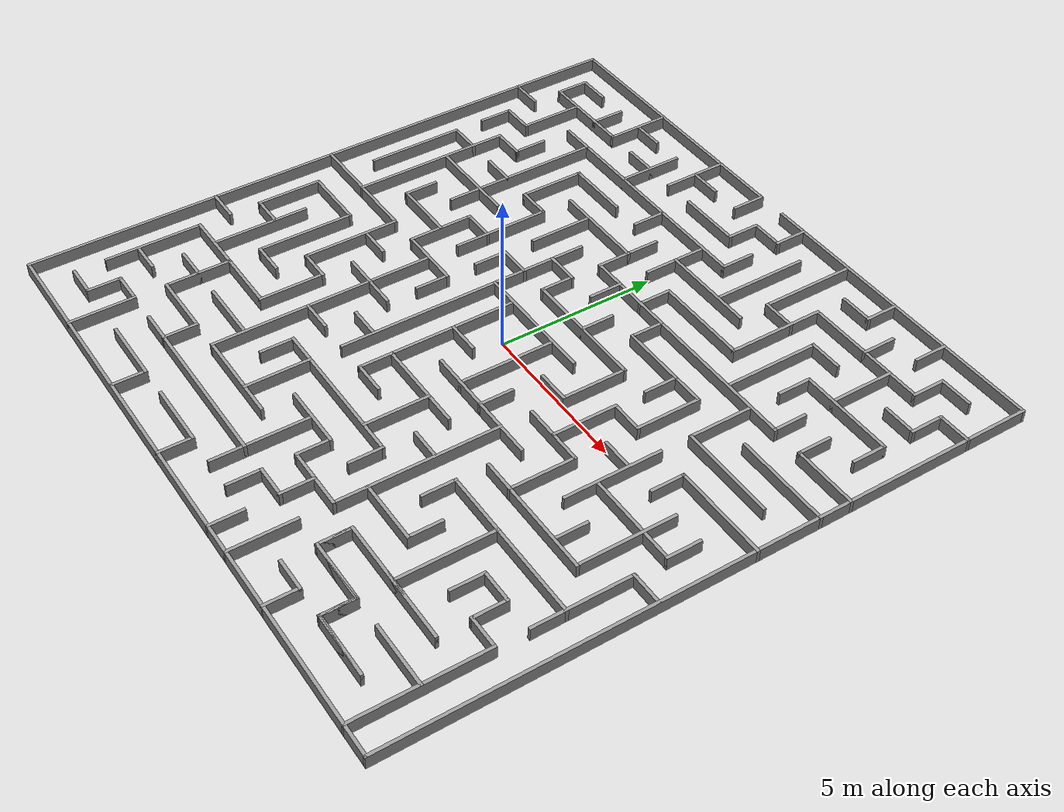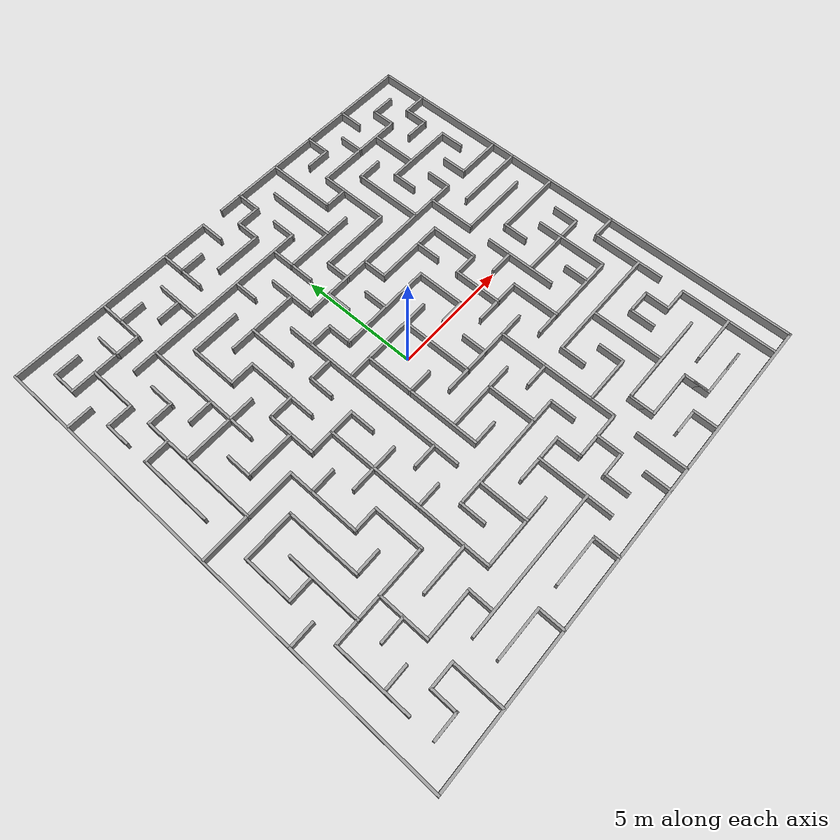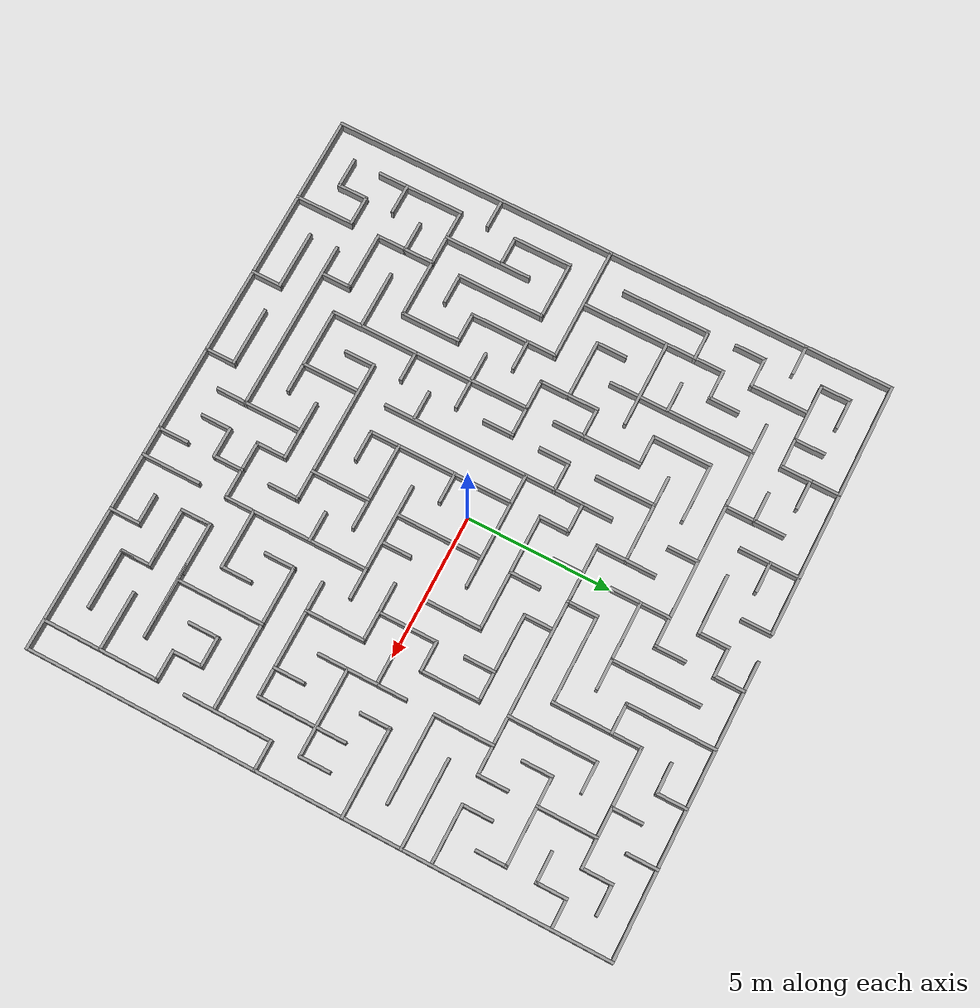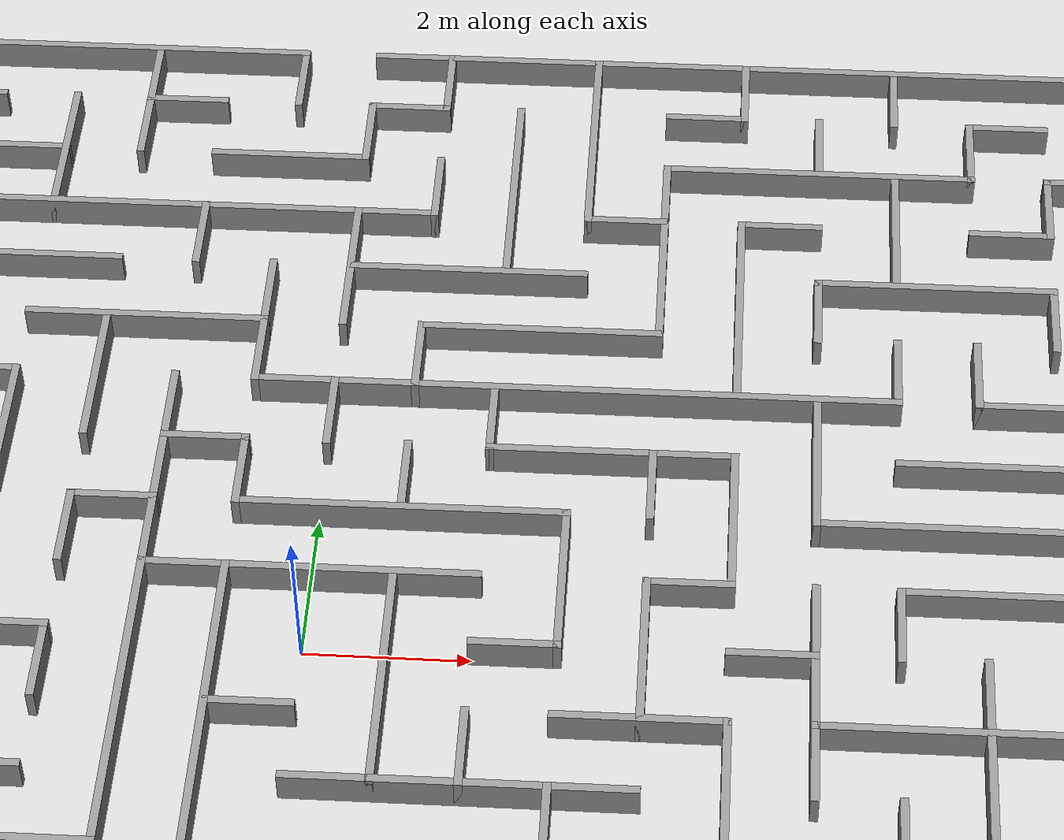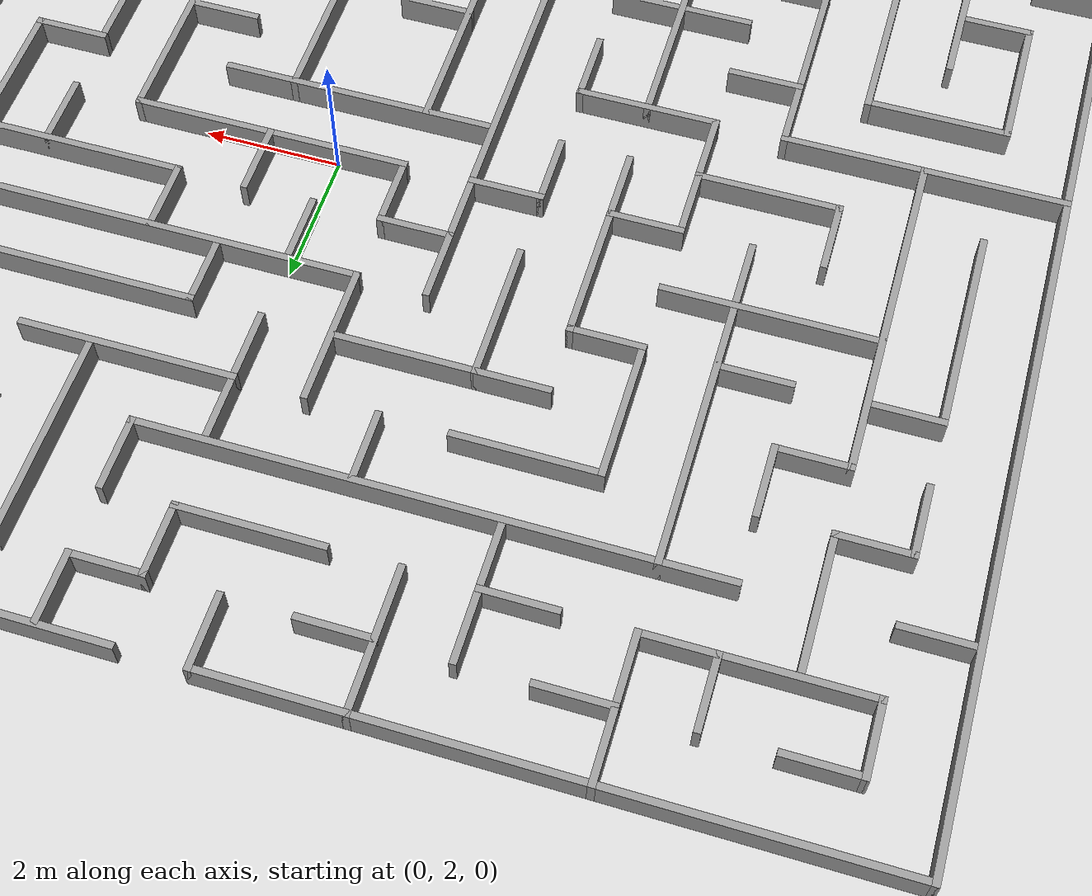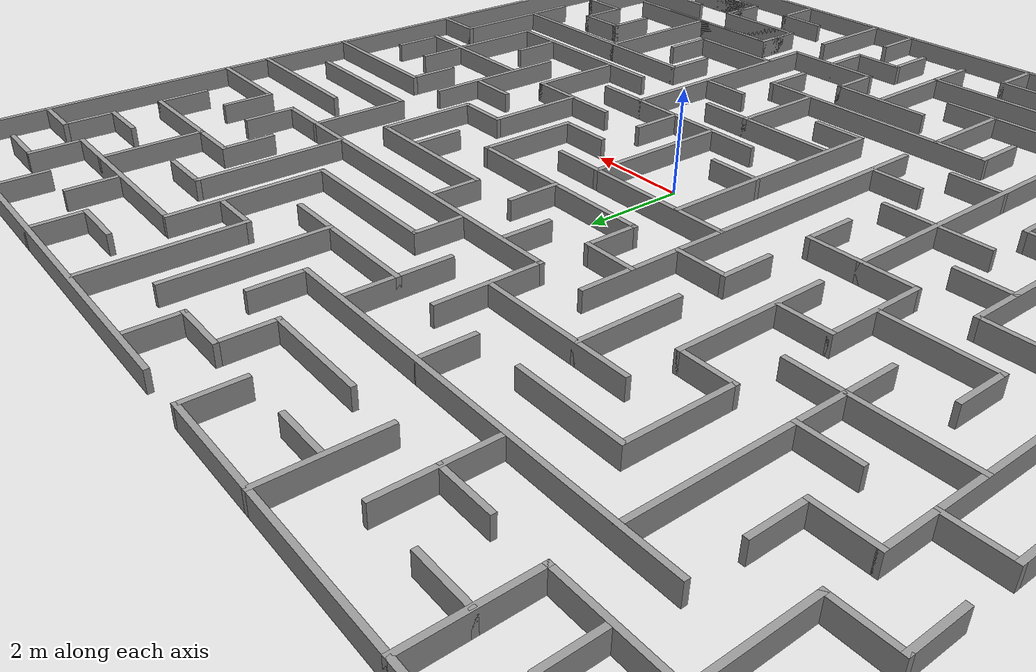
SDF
<?xml version='1.0'?>
<sdf version='1.7'>
  <model name='turtlebot3_maze_3'>
    <pose>0 0 0 0 -0 0</pose>
    <link name='Wall_0'>
      <collision name='Wall_0_Collision'>
        <geometry>
          <box>
            <size>4.1 0.1 0.4</size>
          </box>
        </geometry>
        <pose>0 0 0.2 0 -0 0</pose>
      </collision>
      <visual name='Wall_0_Visual'>
        <pose>0 0 0.2 0 -0 0</pose>
        <geometry>
          <box>
            <size>4.1 0.1 0.4</size>
          </box>
        </geometry>
        <material>
          <script>
            <uri>file://media/materials/scripts/gazebo.material</uri>
            <name>Gazebo/Grey</name>
          </script>
          <ambient>1 1 1 1</ambient>
        </material>
        <meta>
          <layer>0</layer>
        </meta>
      </visual>
      <pose>0 1 0 0 -0 3.14159</pose>
    </link>
    <link name='Wall_10'>
      <collision name='Wall_10_Collision'>
        <geometry>
          <box>
            <size>1.1 0.1 0.4</size>
          </box>
        </geometry>
        <pose>0 0 0.2 0 -0 0</pose>
      </collision>
      <visual name='Wall_10_Visual'>
        <pose>0 0 0.2 0 -0 0</pose>
        <geometry>
          <box>
            <size>1.1 0.1 0.4</size>
          </box>
        </geometry>
        <material>
          <script>
            <uri>file://media/materials/scripts/gazebo.material</uri>
            <name>Gazebo/Grey</name>
          </script>
          <ambient>1 1 1 1</ambient>
        </material>
        <meta>
          <layer>0</layer>
        </meta>
      </visual>
      <pose>-3 1.5 0 0 -0 1.5708</pose>
    </link>
    <link name='Wall_100'>
      <collision name='Wall_100_Collision'>
        <geometry>
          <box>
            <size>4.1 0.1 0.4</size>
          </box>
        </geometry>
        <pose>0 0 0.2 0 -0 0</pose>
      </collision>
      <visual name='Wall_100_Visual'>
        <pose>0 0 0.2 0 -0 0</pose>
        <geometry>
          <box>
            <size>4.1 0.1 0.4</size>
          </box>
        </geometry>
        <material>
          <script>
            <uri>file://media/materials/scripts/gazebo.material</uri>
            <name>Gazebo/Grey</name>
          </script>
          <ambient>1 1 1 1</ambient>
        </material>
        <meta>
          <layer>0</layer>
        </meta>
      </visual>
      <pose>-8 0 0 0 -0 3.14159</pose>
    </link>
    <link name='Wall_102'>
      <collision name='Wall_102_Collision'>
        <geometry>
          <box>
            <size>1.1 0.1 0.4</size>
          </box>
        </geometry>
        <pose>0 0 0.2 0 -0 0</pose>
      </collision>
      <visual name='Wall_102_Visual'>
        <pose>0 0 0.2 0 -0 0</pose>
        <geometry>
          <box>
            <size>1.1 0.1 0.4</size>
          </box>
        </geometry>
        <material>
          <script>
            <uri>file://media/materials/scripts/gazebo.material</uri>
            <name>Gazebo/Grey</name>
          </script>
          <ambient>1 1 1 1</ambient>
        </material>
        <meta>
          <layer>0</layer>
        </meta>
      </visual>
      <pose>-6.5 -4 0 0 -0 3.14159</pose>
    </link>
    <link name='Wall_103'>
      <collision name='Wall_103_Collision'>
        <geometry>
          <box>
            <size>3.1 0.1 0.4</size>
          </box>
        </geometry>
        <pose>0 0 0.2 0 -0 0</pose>
      </collision>
      <visual name='Wall_103_Visual'>
        <pose>0 0 0.2 0 -0 0</pose>
        <geometry>
          <box>
            <size>3.1 0.1 0.4</size>
          </box>
        </geometry>
        <material>
          <script>
            <uri>file://media/materials/scripts/gazebo.material</uri>
            <name>Gazebo/Grey</name>
          </script>
          <ambient>1 1 1 1</ambient>
        </material>
        <meta>
          <layer>0</layer>
        </meta>
      </visual>
      <pose>-7 -2.5 0 0 -0 1.5708</pose>
    </link>
    <link name='Wall_104'>
      <collision name='Wall_104_Collision'>
        <geometry>
          <box>
            <size>2.1 0.1 0.4</size>
          </box>
        </geometry>
        <pose>0 0 0.2 0 -0 0</pose>
      </collision>
      <visual name='Wall_104_Visual'>
        <pose>0 0 0.2 0 -0 0</pose>
        <geometry>
          <box>
            <size>2.1 0.1 0.4</size>
          </box>
        </geometry>
        <material>
          <script>
            <uri>file://media/materials/scripts/gazebo.material</uri>
            <name>Gazebo/Grey</name>
          </script>
          <ambient>1 1 1 1</ambient>
        </material>
        <meta>
          <layer>0</layer>
        </meta>
      </visual>
      <pose>-8 -1 0 0 -0 3.14159</pose>
    </link>
    <link name='Wall_105'>
      <collision name='Wall_105_Collision'>
        <geometry>
          <box>
            <size>2.1 0.1 0.4</size>
          </box>
        </geometry>
        <pose>0 0 0.2 0 -0 0</pose>
      </collision>
      <visual name='Wall_105_Visual'>
        <pose>0 0 0.2 0 -0 0</pose>
        <geometry>
          <box>
            <size>2.1 0.1 0.4</size>
          </box>
        </geometry>
        <material>
          <script>
            <uri>file://media/materials/scripts/gazebo.material</uri>
            <name>Gazebo/Grey</name>
          </script>
          <ambient>1 1 1 1</ambient>
        </material>
        <meta>
          <layer>0</layer>
        </meta>
      </visual>
      <pose>-9 -2 0 0 -0 -1.5708</pose>
    </link>
    <link name='Wall_106'>
      <collision name='Wall_106_Collision'>
        <geometry>
          <box>
            <size>1.1 0.1 0.4</size>
          </box>
        </geometry>
        <pose>0 0 0.2 0 -0 0</pose>
      </collision>
      <visual name='Wall_106_Visual'>
        <pose>0 0 0.2 0 -0 0</pose>
        <geometry>
          <box>
            <size>1.1 0.1 0.4</size>
          </box>
        </geometry>
        <material>
          <script>
            <uri>file://media/materials/scripts/gazebo.material</uri>
            <name>Gazebo/Grey</name>
          </script>
          <ambient>1 1 1 1</ambient>
        </material>
        <meta>
          <layer>0</layer>
        </meta>
      </visual>
      <pose>-8.5 -3 0 0 -0 0</pose>
    </link>
    <link name='Wall_108'>
      <collision name='Wall_108_Collision'>
        <geometry>
          <box>
            <size>3.1 0.1 0.4</size>
          </box>
        </geometry>
        <pose>0 0 0.2 0 -0 0</pose>
      </collision>
      <visual name='Wall_108_Visual'>
        <pose>0 0 0.2 0 -0 0</pose>
        <geometry>
          <box>
            <size>3.1 0.1 0.4</size>
          </box>
        </geometry>
        <material>
          <script>
            <uri>file://media/materials/scripts/gazebo.material</uri>
            <name>Gazebo/Grey</name>
          </script>
          <ambient>1 1 1 1</ambient>
        </material>
        <meta>
          <layer>0</layer>
        </meta>
      </visual>
      <pose>-8 -3.5 0 0 -0 -1.5708</pose>
    </link>
    <link name='Wall_11'>
      <collision name='Wall_11_Collision'>
        <geometry>
          <box>
            <size>1.1 0.1 0.4</size>
          </box>
        </geometry>
        <pose>0 0 0.2 0 -0 0</pose>
      </collision>
      <visual name='Wall_11_Visual'>
        <pose>0 0 0.2 0 -0 0</pose>
        <geometry>
          <box>
            <size>1.1 0.1 0.4</size>
          </box>
        </geometry>
        <material>
          <script>
            <uri>file://media/materials/scripts/gazebo.material</uri>
            <name>Gazebo/Grey</name>
          </script>
          <ambient>1 1 1 1</ambient>
        </material>
        <meta>
          <layer>0</layer>
        </meta>
      </visual>
      <pose>-2.5 2 0 0 -0 0</pose>
    </link>
    <link name='Wall_110'>
      <collision name='Wall_110_Collision'>
        <geometry>
          <box>
            <size>1.1 0.1 0.4</size>
          </box>
        </geometry>
        <pose>0 0 0.2 0 -0 0</pose>
      </collision>
      <visual name='Wall_110_Visual'>
        <pose>0 0 0.2 0 -0 0</pose>
        <geometry>
          <box>
            <size>1.1 0.1 0.4</size>
          </box>
        </geometry>
        <material>
          <script>
            <uri>file://media/materials/scripts/gazebo.material</uri>
            <name>Gazebo/Grey</name>
          </script>
          <ambient>1 1 1 1</ambient>
        </material>
        <meta>
          <layer>0</layer>
        </meta>
      </visual>
      <pose>-9.5 -4 0 0 -0 0</pose>
    </link>
    <link name='Wall_112'>
      <collision name='Wall_112_Collision'>
        <geometry>
          <box>
            <size>1.1 0.1 0.4</size>
          </box>
        </geometry>
        <pose>0 0 0.2 0 -0 0</pose>
      </collision>
      <visual name='Wall_112_Visual'>
        <pose>0 0 0.2 0 -0 0</pose>
        <geometry>
          <box>
            <size>1.1 0.1 0.4</size>
          </box>
        </geometry>
        <material>
          <script>
            <uri>file://media/materials/scripts/gazebo.material</uri>
            <name>Gazebo/Grey</name>
          </script>
          <ambient>1 1 1 1</ambient>
        </material>
        <meta>
          <layer>0</layer>
        </meta>
      </visual>
      <pose>-8.5 -7 0 0 -0 0</pose>
    </link>
    <link name='Wall_114'>
      <collision name='Wall_114_Collision'>
        <geometry>
          <box>
            <size>2.1 0.1 0.4</size>
          </box>
        </geometry>
        <pose>0 0 0.2 0 -0 0</pose>
      </collision>
      <visual name='Wall_114_Visual'>
        <pose>0 0 0.2 0 -0 0</pose>
        <geometry>
          <box>
            <size>2.1 0.1 0.4</size>
          </box>
        </geometry>
        <material>
          <script>
            <uri>file://media/materials/scripts/gazebo.material</uri>
            <name>Gazebo/Grey</name>
          </script>
          <ambient>1 1 1 1</ambient>
        </material>
        <meta>
          <layer>0</layer>
        </meta>
      </visual>
      <pose>-7 -6 0 0 -0 -1.5708</pose>
    </link>
    <link name='Wall_115'>
      <collision name='Wall_115_Collision'>
        <geometry>
          <box>
            <size>2.1 0.1 0.4</size>
          </box>
        </geometry>
        <pose>0 0 0.2 0 -0 0</pose>
      </collision>
      <visual name='Wall_115_Visual'>
        <pose>0 0 0.2 0 -0 0</pose>
        <geometry>
          <box>
            <size>2.1 0.1 0.4</size>
          </box>
        </geometry>
        <material>
          <script>
            <uri>file://media/materials/scripts/gazebo.material</uri>
            <name>Gazebo/Grey</name>
          </script>
          <ambient>1 1 1 1</ambient>
        </material>
        <meta>
          <layer>0</layer>
        </meta>
      </visual>
      <pose>-6 -7 0 0 -0 0</pose>
    </link>
    <link name='Wall_116'>
      <collision name='Wall_116_Collision'>
        <geometry>
          <box>
            <size>1.1 0.1 0.4</size>
          </box>
        </geometry>
        <pose>0 0 0.2 0 -0 0</pose>
      </collision>
      <visual name='Wall_116_Visual'>
        <pose>0 0 0.2 0 -0 0</pose>
        <geometry>
          <box>
            <size>1.1 0.1 0.4</size>
          </box>
        </geometry>
        <material>
          <script>
            <uri>file://media/materials/scripts/gazebo.material</uri>
            <name>Gazebo/Grey</name>
          </script>
          <ambient>1 1 1 1</ambient>
        </material>
        <meta>
          <layer>0</layer>
        </meta>
      </visual>
      <pose>-5 -7.5 0 0 -0 -1.5708</pose>
    </link>
    <link name='Wall_118'>
      <collision name='Wall_118_Collision'>
        <geometry>
          <box>
            <size>1.1 0.1 0.4</size>
          </box>
        </geometry>
        <pose>0 0 0.2 0 -0 0</pose>
      </collision>
      <visual name='Wall_118_Visual'>
        <pose>0 0 0.2 0 -0 0</pose>
        <geometry>
          <box>
            <size>1.1 0.1 0.4</size>
          </box>
        </geometry>
        <material>
          <script>
            <uri>file://media/materials/scripts/gazebo.material</uri>
            <name>Gazebo/Grey</name>
          </script>
          <ambient>1 1 1 1</ambient>
        </material>
        <meta>
          <layer>0</layer>
        </meta>
      </visual>
      <pose>-7.5 -6 0 0 -0 0</pose>
    </link>
    <link name='Wall_120'>
      <collision name='Wall_120_Collision'>
        <geometry>
          <box>
            <size>2.1 0.1 0.4</size>
          </box>
        </geometry>
        <pose>0 0 0.2 0 -0 0</pose>
      </collision>
      <visual name='Wall_120_Visual'>
        <pose>0 0 0.2 0 -0 0</pose>
        <geometry>
          <box>
            <size>2.1 0.1 0.4</size>
          </box>
        </geometry>
        <material>
          <script>
            <uri>file://media/materials/scripts/gazebo.material</uri>
            <name>Gazebo/Grey</name>
          </script>
          <ambient>1 1 1 1</ambient>
        </material>
        <meta>
          <layer>0</layer>
        </meta>
      </visual>
      <pose>-5 -6 0 0 -0 0</pose>
    </link>
    <link name='Wall_122'>
      <collision name='Wall_122_Collision'>
        <geometry>
          <box>
            <size>1.10012 0.1 0.4</size>
          </box>
        </geometry>
        <pose>0 0 0.2 0 -0 0</pose>
      </collision>
      <visual name='Wall_122_Visual'>
        <pose>0 0 0.2 0 -0 0</pose>
        <geometry>
          <box>
            <size>1.10012 0.1 0.4</size>
          </box>
        </geometry>
        <material>
          <script>
            <uri>file://media/materials/scripts/gazebo.material</uri>
            <name>Gazebo/Grey</name>
          </script>
          <ambient>1 1 1 1</ambient>
        </material>
        <meta>
          <layer>0</layer>
        </meta>
      </visual>
      <pose>-3 -0.5 0 0 -0 1.5708</pose>
    </link>
    <link name='Wall_123'>
      <collision name='Wall_123_Collision'>
        <geometry>
          <box>
            <size>2.1 0.1 0.4</size>
          </box>
        </geometry>
        <pose>0 0 0.2 0 -0 0</pose>
      </collision>
      <visual name='Wall_123_Visual'>
        <pose>0 0 0.2 0 -0 0</pose>
        <geometry>
          <box>
            <size>2.1 0.1 0.4</size>
          </box>
        </geometry>
        <material>
          <script>
            <uri>file://media/materials/scripts/gazebo.material</uri>
            <name>Gazebo/Grey</name>
          </script>
          <ambient>1 1 1 1</ambient>
        </material>
        <meta>
          <layer>0</layer>
        </meta>
      </visual>
      <pose>-4 0 0 0 -0 3.14159</pose>
    </link>
    <link name='Wall_124'>
      <collision name='Wall_124_Collision'>
        <geometry>
          <box>
            <size>2.1 0.1 0.4</size>
          </box>
        </geometry>
        <pose>0 0 0.2 0 -0 0</pose>
      </collision>
      <visual name='Wall_124_Visual'>
        <pose>0 0 0.2 0 -0 0</pose>
        <geometry>
          <box>
            <size>2.1 0.1 0.4</size>
          </box>
        </geometry>
        <material>
          <script>
            <uri>file://media/materials/scripts/gazebo.material</uri>
            <name>Gazebo/Grey</name>
          </script>
          <ambient>1 1 1 1</ambient>
        </material>
        <meta>
          <layer>0</layer>
        </meta>
      </visual>
      <pose>-5 1 0 0 -0 1.5708</pose>
    </link>
    <link name='Wall_125'>
      <collision name='Wall_125_Collision'>
        <geometry>
          <box>
            <size>1.1 0.1 0.4</size>
          </box>
        </geometry>
        <pose>0 0 0.2 0 -0 0</pose>
      </collision>
      <visual name='Wall_125_Visual'>
        <pose>0 0 0.2 0 -0 0</pose>
        <geometry>
          <box>
            <size>1.1 0.1 0.4</size>
          </box>
        </geometry>
        <material>
          <script>
            <uri>file://media/materials/scripts/gazebo.material</uri>
            <name>Gazebo/Grey</name>
          </script>
          <ambient>1 1 1 1</ambient>
        </material>
        <meta>
          <layer>0</layer>
        </meta>
      </visual>
      <pose>-4.5 2 0 0 -0 0</pose>
    </link>
    <link name='Wall_127'>
      <collision name='Wall_127_Collision'>
        <geometry>
          <box>
            <size>1.1 0.1 0.4</size>
          </box>
        </geometry>
        <pose>0 0 0.2 0 -0 0</pose>
      </collision>
      <visual name='Wall_127_Visual'>
        <pose>0 0 0.2 0 -0 0</pose>
        <geometry>
          <box>
            <size>1.1 0.1 0.4</size>
          </box>
        </geometry>
        <material>
          <script>
            <uri>file://media/materials/scripts/gazebo.material</uri>
            <name>Gazebo/Grey</name>
          </script>
          <ambient>1 1 1 1</ambient>
        </material>
        <meta>
          <layer>0</layer>
        </meta>
      </visual>
      <pose>-7 1.5 0 0 -0 -1.5708</pose>
    </link>
    <link name='Wall_128'>
      <collision name='Wall_128_Collision'>
        <geometry>
          <box>
            <size>2.1 0.1 0.4</size>
          </box>
        </geometry>
        <pose>0 0 0.2 0 -0 0</pose>
      </collision>
      <visual name='Wall_128_Visual'>
        <pose>0 0 0.2 0 -0 0</pose>
        <geometry>
          <box>
            <size>2.1 0.1 0.4</size>
          </box>
        </geometry>
        <material>
          <script>
            <uri>file://media/materials/scripts/gazebo.material</uri>
            <name>Gazebo/Grey</name>
          </script>
          <ambient>1 1 1 1</ambient>
        </material>
        <meta>
          <layer>0</layer>
        </meta>
      </visual>
      <pose>-6 1 0 0 -0 0</pose>
    </link>
    <link name='Wall_13'>
      <collision name='Wall_13_Collision'>
        <geometry>
          <box>
            <size>1.1 0.1 0.4</size>
          </box>
        </geometry>
        <pose>0 0 0.2 0 -0 0</pose>
      </collision>
      <visual name='Wall_13_Visual'>
        <pose>0 0 0.2 0 -0 0</pose>
        <geometry>
          <box>
            <size>1.1 0.1 0.4</size>
          </box>
        </geometry>
        <material>
          <script>
            <uri>file://media/materials/scripts/gazebo.material</uri>
            <name>Gazebo/Grey</name>
          </script>
          <ambient>1 1 1 1</ambient>
        </material>
        <meta>
          <layer>0</layer>
        </meta>
      </visual>
      <pose>-2.5 -3 0 0 -0 0</pose>
    </link>
    <link name='Wall_130'>
      <collision name='Wall_130_Collision'>
        <geometry>
          <box>
            <size>5.1 0.1 0.4</size>
          </box>
        </geometry>
        <pose>0 0 0.2 0 -0 0</pose>
      </collision>
      <visual name='Wall_130_Visual'>
        <pose>0 0 0.2 0 -0 0</pose>
        <geometry>
          <box>
            <size>5.1 0.1 0.4</size>
          </box>
        </geometry>
        <material>
          <script>
            <uri>file://media/materials/scripts/gazebo.material</uri>
            <name>Gazebo/Grey</name>
          </script>
          <ambient>1 1 1 1</ambient>
        </material>
        <meta>
          <layer>0</layer>
        </meta>
      </visual>
      <pose>-8 2.5 0 0 -0 1.5708</pose>
    </link>
    <link name='Wall_131'>
      <collision name='Wall_131_Collision'>
        <geometry>
          <box>
            <size>1.1 0.1 0.4</size>
          </box>
        </geometry>
        <pose>0 0 0.2 0 -0 0</pose>
      </collision>
      <visual name='Wall_131_Visual'>
        <pose>0 0 0.2 0 -0 0</pose>
        <geometry>
          <box>
            <size>1.1 0.1 0.4</size>
          </box>
        </geometry>
        <material>
          <script>
            <uri>file://media/materials/scripts/gazebo.material</uri>
            <name>Gazebo/Grey</name>
          </script>
          <ambient>1 1 1 1</ambient>
        </material>
        <meta>
          <layer>0</layer>
        </meta>
      </visual>
      <pose>-7.5 5 0 0 -0 0</pose>
    </link>
    <link name='Wall_132'>
      <collision name='Wall_132_Collision'>
        <geometry>
          <box>
            <size>1.1 0.1 0.4</size>
          </box>
        </geometry>
        <pose>0 0 0.2 0 -0 0</pose>
      </collision>
      <visual name='Wall_132_Visual'>
        <pose>0 0 0.2 0 -0 0</pose>
        <geometry>
          <box>
            <size>1.1 0.1 0.4</size>
          </box>
        </geometry>
        <material>
          <script>
            <uri>file://media/materials/scripts/gazebo.material</uri>
            <name>Gazebo/Grey</name>
          </script>
          <ambient>1 1 1 1</ambient>
        </material>
        <meta>
          <layer>0</layer>
        </meta>
      </visual>
      <pose>-7 5.5 0 0 -0 1.5708</pose>
    </link>
    <link name='Wall_134'>
      <collision name='Wall_134_Collision'>
        <geometry>
          <box>
            <size>1.1 0.1 0.4</size>
          </box>
        </geometry>
        <pose>0 0 0.2 0 -0 0</pose>
      </collision>
      <visual name='Wall_134_Visual'>
        <pose>0 0 0.2 0 -0 0</pose>
        <geometry>
          <box>
            <size>1.1 0.1 0.4</size>
          </box>
        </geometry>
        <material>
          <script>
            <uri>file://media/materials/scripts/gazebo.material</uri>
            <name>Gazebo/Grey</name>
          </script>
          <ambient>1 1 1 1</ambient>
        </material>
        <meta>
          <layer>0</layer>
        </meta>
      </visual>
      <pose>-8.5 4 0 0 -0 3.14159</pose>
    </link>
    <link name='Wall_135'>
      <collision name='Wall_135_Collision'>
        <geometry>
          <box>
            <size>3.1 0.1 0.4</size>
          </box>
        </geometry>
        <pose>0 0 0.2 0 -0 0</pose>
      </collision>
      <visual name='Wall_135_Visual'>
        <pose>0 0 0.2 0 -0 0</pose>
        <geometry>
          <box>
            <size>3.1 0.1 0.4</size>
          </box>
        </geometry>
        <material>
          <script>
            <uri>file://media/materials/scripts/gazebo.material</uri>
            <name>Gazebo/Grey</name>
          </script>
          <ambient>1 1 1 1</ambient>
        </material>
        <meta>
          <layer>0</layer>
        </meta>
      </visual>
      <pose>-9 2.5 0 0 -0 -1.5708</pose>
    </link>
    <link name='Wall_137'>
      <collision name='Wall_137_Collision'>
        <geometry>
          <box>
            <size>3.1 0.1 0.4</size>
          </box>
        </geometry>
        <pose>0 0 0.2 0 -0 0</pose>
      </collision>
      <visual name='Wall_137_Visual'>
        <pose>0 0 0.2 0 -0 0</pose>
        <geometry>
          <box>
            <size>3.1 0.1 0.4</size>
          </box>
        </geometry>
        <material>
          <script>
            <uri>file://media/materials/scripts/gazebo.material</uri>
            <name>Gazebo/Grey</name>
          </script>
          <ambient>1 1 1 1</ambient>
        </material>
        <meta>
          <layer>0</layer>
        </meta>
      </visual>
      <pose>-6.5 3 0 0 -0 0</pose>
    </link>
    <link name='Wall_139'>
      <collision name='Wall_139_Collision'>
        <geometry>
          <box>
            <size>5.1 0.1 0.4</size>
          </box>
        </geometry>
        <pose>0 0 0.2 0 -0 0</pose>
      </collision>
      <visual name='Wall_139_Visual'>
        <pose>0 0 0.2 0 -0 0</pose>
        <geometry>
          <box>
            <size>5.1 0.1 0.4</size>
          </box>
        </geometry>
        <material>
          <script>
            <uri>file://media/materials/scripts/gazebo.material</uri>
            <name>Gazebo/Grey</name>
          </script>
          <ambient>1 1 1 1</ambient>
        </material>
        <meta>
          <layer>0</layer>
        </meta>
      </visual>
      <pose>-6 4.5 0 0 -0 1.5708</pose>
    </link>
    <link name='Wall_141'>
      <collision name='Wall_141_Collision'>
        <geometry>
          <box>
            <size>1.1 0.1 0.4</size>
          </box>
        </geometry>
        <pose>0 0 0.2 0 -0 0</pose>
      </collision>
      <visual name='Wall_141_Visual'>
        <pose>0 0 0.2 0 -0 0</pose>
        <geometry>
          <box>
            <size>1.1 0.1 0.4</size>
          </box>
        </geometry>
        <material>
          <script>
            <uri>file://media/materials/scripts/gazebo.material</uri>
            <name>Gazebo/Grey</name>
          </script>
          <ambient>1 1 1 1</ambient>
        </material>
        <meta>
          <layer>0</layer>
        </meta>
      </visual>
      <pose>-6.5 4 0 0 -0 0</pose>
    </link>
    <link name='Wall_143'>
      <collision name='Wall_143_Collision'>
        <geometry>
          <box>
            <size>8.1 0.1 0.4</size>
          </box>
        </geometry>
        <pose>0 0 0.2 0 -0 0</pose>
      </collision>
      <visual name='Wall_143_Visual'>
        <pose>0 0 0.2 0 -0 0</pose>
        <geometry>
          <box>
            <size>8.1 0.1 0.4</size>
          </box>
        </geometry>
        <material>
          <script>
            <uri>file://media/materials/scripts/gazebo.material</uri>
            <name>Gazebo/Grey</name>
          </script>
          <ambient>1 1 1 1</ambient>
        </material>
        <meta>
          <layer>0</layer>
        </meta>
      </visual>
      <pose>-3 7 0 0 -0 0</pose>
    </link>
    <link name='Wall_144'>
      <collision name='Wall_144_Collision'>
        <geometry>
          <box>
            <size>1.1 0.1 0.4</size>
          </box>
        </geometry>
        <pose>0 0 0.2 0 -0 0</pose>
      </collision>
      <visual name='Wall_144_Visual'>
        <pose>0 0 0.2 0 -0 0</pose>
        <geometry>
          <box>
            <size>1.1 0.1 0.4</size>
          </box>
        </geometry>
        <material>
          <script>
            <uri>file://media/materials/scripts/gazebo.material</uri>
            <name>Gazebo/Grey</name>
          </script>
          <ambient>1 1 1 1</ambient>
        </material>
        <meta>
          <layer>0</layer>
        </meta>
      </visual>
      <pose>1 7.5 0 0 -0 1.5708</pose>
    </link>
    <link name='Wall_146'>
      <collision name='Wall_146_Collision'>
        <geometry>
          <box>
            <size>2.1 0.1 0.4</size>
          </box>
        </geometry>
        <pose>0 0 0.2 0 -0 0</pose>
      </collision>
      <visual name='Wall_146_Visual'>
        <pose>0 0 0.2 0 -0 0</pose>
        <geometry>
          <box>
            <size>2.1 0.1 0.4</size>
          </box>
        </geometry>
        <material>
          <script>
            <uri>file://media/materials/scripts/gazebo.material</uri>
            <name>Gazebo/Grey</name>
          </script>
          <ambient>1 1 1 1</ambient>
        </material>
        <meta>
          <layer>0</layer>
        </meta>
      </visual>
      <pose>-4 6 0 0 -0 3.14159</pose>
    </link>
    <link name='Wall_148'>
      <collision name='Wall_148_Collision'>
        <geometry>
          <box>
            <size>1.1 0.1 0.4</size>
          </box>
        </geometry>
        <pose>0 0 0.2 0 -0 0</pose>
      </collision>
      <visual name='Wall_148_Visual'>
        <pose>0 0 0.2 0 -0 0</pose>
        <geometry>
          <box>
            <size>1.1 0.1 0.4</size>
          </box>
        </geometry>
        <material>
          <script>
            <uri>file://media/materials/scripts/gazebo.material</uri>
            <name>Gazebo/Grey</name>
          </script>
          <ambient>1 1 1 1</ambient>
        </material>
        <meta>
          <layer>0</layer>
        </meta>
      </visual>
      <pose>-4.5 4 0 0 -0 0</pose>
    </link>
    <link name='Wall_149'>
      <collision name='Wall_149_Collision'>
        <geometry>
          <box>
            <size>3.1 0.1 0.4</size>
          </box>
        </geometry>
        <pose>0 0 0.2 0 -0 0</pose>
      </collision>
      <visual name='Wall_149_Visual'>
        <pose>0 0 0.2 0 -0 0</pose>
        <geometry>
          <box>
            <size>3.1 0.1 0.4</size>
          </box>
        </geometry>
        <material>
          <script>
            <uri>file://media/materials/scripts/gazebo.material</uri>
            <name>Gazebo/Grey</name>
          </script>
          <ambient>1 1 1 1</ambient>
        </material>
        <meta>
          <layer>0</layer>
        </meta>
      </visual>
      <pose>-4 2.5 0 0 -0 -1.5708</pose>
    </link>
    <link name='Wall_15'>
      <collision name='Wall_15_Collision'>
        <geometry>
          <box>
            <size>1.1 0.1 0.4</size>
          </box>
        </geometry>
        <pose>0 0 0.2 0 -0 0</pose>
      </collision>
      <visual name='Wall_15_Visual'>
        <pose>0 0 0.2 0 -0 0</pose>
        <geometry>
          <box>
            <size>1.1 0.1 0.4</size>
          </box>
        </geometry>
        <material>
          <script>
            <uri>file://media/materials/scripts/gazebo.material</uri>
            <name>Gazebo/Grey</name>
          </script>
          <ambient>1 1 1 1</ambient>
        </material>
        <meta>
          <layer>0</layer>
        </meta>
      </visual>
      <pose>-0.5 -1 0 0 -0 3.14159</pose>
    </link>
    <link name='Wall_151'>
      <collision name='Wall_151_Collision'>
        <geometry>
          <box>
            <size>2.1 0.1 0.4</size>
          </box>
        </geometry>
        <pose>0 0 0.2 0 -0 0</pose>
      </collision>
      <visual name='Wall_151_Visual'>
        <pose>0 0 0.2 0 -0 0</pose>
        <geometry>
          <box>
            <size>2.1 0.1 0.4</size>
          </box>
        </geometry>
        <material>
          <script>
            <uri>file://media/materials/scripts/gazebo.material</uri>
            <name>Gazebo/Grey</name>
          </script>
          <ambient>1 1 1 1</ambient>
        </material>
        <meta>
          <layer>0</layer>
        </meta>
      </visual>
      <pose>-3 4 0 0 -0 1.5708</pose>
    </link>
    <link name='Wall_153'>
      <collision name='Wall_153_Collision'>
        <geometry>
          <box>
            <size>1.1 0.1 0.4</size>
          </box>
        </geometry>
        <pose>0 0 0.2 0 -0 0</pose>
      </collision>
      <visual name='Wall_153_Visual'>
        <pose>0 0 0.2 0 -0 0</pose>
        <geometry>
          <box>
            <size>1.1 0.1 0.4</size>
          </box>
        </geometry>
        <material>
          <script>
            <uri>file://media/materials/scripts/gazebo.material</uri>
            <name>Gazebo/Grey</name>
          </script>
          <ambient>1 1 1 1</ambient>
        </material>
        <meta>
          <layer>0</layer>
        </meta>
      </visual>
      <pose>7 4.5 0 0 -0 -1.5708</pose>
    </link>
    <link name='Wall_154'>
      <collision name='Wall_154_Collision'>
        <geometry>
          <box>
            <size>8.1 0.1 0.4</size>
          </box>
        </geometry>
        <pose>0 0 0.2 0 -0 0</pose>
      </collision>
      <visual name='Wall_154_Visual'>
        <pose>0 0 0.2 0 -0 0</pose>
        <geometry>
          <box>
            <size>8.1 0.1 0.4</size>
          </box>
        </geometry>
        <material>
          <script>
            <uri>file://media/materials/scripts/gazebo.material</uri>
            <name>Gazebo/Grey</name>
          </script>
          <ambient>1 1 1 1</ambient>
        </material>
        <meta>
          <layer>0</layer>
        </meta>
      </visual>
      <pose>3 4 0 0 -0 3.14159</pose>
    </link>
    <link name='Wall_155'>
      <collision name='Wall_155_Collision'>
        <geometry>
          <box>
            <size>2.1 0.1 0.4</size>
          </box>
        </geometry>
        <pose>0 0 0.2 0 -0 0</pose>
      </collision>
      <visual name='Wall_155_Visual'>
        <pose>0 0 0.2 0 -0 0</pose>
        <geometry>
          <box>
            <size>2.1 0.1 0.4</size>
          </box>
        </geometry>
        <material>
          <script>
            <uri>file://media/materials/scripts/gazebo.material</uri>
            <name>Gazebo/Grey</name>
          </script>
          <ambient>1 1 1 1</ambient>
        </material>
        <meta>
          <layer>0</layer>
        </meta>
      </visual>
      <pose>-1 5 0 0 -0 1.5708</pose>
    </link>
    <link name='Wall_157'>
      <collision name='Wall_157_Collision'>
        <geometry>
          <box>
            <size>3.1 0.1 0.4</size>
          </box>
        </geometry>
        <pose>0 0 0.2 0 -0 0</pose>
      </collision>
      <visual name='Wall_157_Visual'>
        <pose>0 0 0.2 0 -0 0</pose>
        <geometry>
          <box>
            <size>3.1 0.1 0.4</size>
          </box>
        </geometry>
        <material>
          <script>
            <uri>file://media/materials/scripts/gazebo.material</uri>
            <name>Gazebo/Grey</name>
          </script>
          <ambient>1 1 1 1</ambient>
        </material>
        <meta>
          <layer>0</layer>
        </meta>
      </visual>
      <pose>-2.5 5 0 0 -0 0</pose>
    </link>
    <link name='Wall_159'>
      <collision name='Wall_159_Collision'>
        <geometry>
          <box>
            <size>1.1 0.1 0.4</size>
          </box>
        </geometry>
        <pose>0 0 0.2 0 -0 0</pose>
      </collision>
      <visual name='Wall_159_Visual'>
        <pose>0 0 0.2 0 -0 0</pose>
        <geometry>
          <box>
            <size>1.1 0.1 0.4</size>
          </box>
        </geometry>
        <material>
          <script>
            <uri>file://media/materials/scripts/gazebo.material</uri>
            <name>Gazebo/Grey</name>
          </script>
          <ambient>1 1 1 1</ambient>
        </material>
        <meta>
          <layer>0</layer>
        </meta>
      </visual>
      <pose>-9.5 7 0 0 -0 0</pose>
    </link>
    <link name='Wall_161'>
      <collision name='Wall_161_Collision'>
        <geometry>
          <box>
            <size>1.1 0.1 0.4</size>
          </box>
        </geometry>
        <pose>0 0 0.2 0 -0 0</pose>
      </collision>
      <visual name='Wall_161_Visual'>
        <pose>0 0 0.2 0 -0 0</pose>
        <geometry>
          <box>
            <size>1.1 0.1 0.4</size>
          </box>
        </geometry>
        <material>
          <script>
            <uri>file://media/materials/scripts/gazebo.material</uri>
            <name>Gazebo/Grey</name>
          </script>
          <ambient>1 1 1 1</ambient>
        </material>
        <meta>
          <layer>0</layer>
        </meta>
      </visual>
      <pose>-8.5 9 0 0 -0 3.14159</pose>
    </link>
    <link name='Wall_162'>
      <collision name='Wall_162_Collision'>
        <geometry>
          <box>
            <size>1.1 0.1 0.4</size>
          </box>
        </geometry>
        <pose>0 0 0.2 0 -0 0</pose>
      </collision>
      <visual name='Wall_162_Visual'>
        <pose>0 0 0.2 0 -0 0</pose>
        <geometry>
          <box>
            <size>1.1 0.1 0.4</size>
          </box>
        </geometry>
        <material>
          <script>
            <uri>file://media/materials/scripts/gazebo.material</uri>
            <name>Gazebo/Grey</name>
          </script>
          <ambient>1 1 1 1</ambient>
        </material>
        <meta>
          <layer>0</layer>
        </meta>
      </visual>
      <pose>-9 8.5 0 0 -0 -1.5708</pose>
    </link>
    <link name='Wall_163'>
      <collision name='Wall_163_Collision'>
        <geometry>
          <box>
            <size>3.1 0.1 0.4</size>
          </box>
        </geometry>
        <pose>0 0 0.2 0 -0 0</pose>
      </collision>
      <visual name='Wall_163_Visual'>
        <pose>0 0 0.2 0 -0 0</pose>
        <geometry>
          <box>
            <size>3.1 0.1 0.4</size>
          </box>
        </geometry>
        <material>
          <script>
            <uri>file://media/materials/scripts/gazebo.material</uri>
            <name>Gazebo/Grey</name>
          </script>
          <ambient>1 1 1 1</ambient>
        </material>
        <meta>
          <layer>0</layer>
        </meta>
      </visual>
      <pose>-7.5 8 0 0 -0 0</pose>
    </link>
    <link name='Wall_164'>
      <collision name='Wall_164_Collision'>
        <geometry>
          <box>
            <size>2.1 0.1 0.4</size>
          </box>
        </geometry>
        <pose>0 0 0.2 0 -0 0</pose>
      </collision>
      <visual name='Wall_164_Visual'>
        <pose>0 0 0.2 0 -0 0</pose>
        <geometry>
          <box>
            <size>2.1 0.1 0.4</size>
          </box>
        </geometry>
        <material>
          <script>
            <uri>file://media/materials/scripts/gazebo.material</uri>
            <name>Gazebo/Grey</name>
          </script>
          <ambient>1 1 1 1</ambient>
        </material>
        <meta>
          <layer>0</layer>
        </meta>
      </visual>
      <pose>-6 9 0 0 -0 1.5708</pose>
    </link>
    <link name='Wall_166'>
      <collision name='Wall_166_Collision'>
        <geometry>
          <box>
            <size>1.1 0.1 0.4</size>
          </box>
        </geometry>
        <pose>0 0 0.2 0 -0 0</pose>
      </collision>
      <visual name='Wall_166_Visual'>
        <pose>0 0 0.2 0 -0 0</pose>
        <geometry>
          <box>
            <size>1.1 0.1 0.4</size>
          </box>
        </geometry>
        <material>
          <script>
            <uri>file://media/materials/scripts/gazebo.material</uri>
            <name>Gazebo/Grey</name>
          </script>
          <ambient>1 1 1 1</ambient>
        </material>
        <meta>
          <layer>0</layer>
        </meta>
      </visual>
      <pose>-7 8.5 0 0 -0 -1.5708</pose>
    </link>
    <link name='Wall_168'>
      <collision name='Wall_168_Collision'>
        <geometry>
          <box>
            <size>2.1 0.1 0.4</size>
          </box>
        </geometry>
        <pose>0 0 0.2 0 -0 0</pose>
      </collision>
      <visual name='Wall_168_Visual'>
        <pose>0 0 0.2 0 -0 0</pose>
        <geometry>
          <box>
            <size>2.1 0.1 0.4</size>
          </box>
        </geometry>
        <material>
          <script>
            <uri>file://media/materials/scripts/gazebo.material</uri>
            <name>Gazebo/Grey</name>
          </script>
          <ambient>1 1 1 1</ambient>
        </material>
        <meta>
          <layer>0</layer>
        </meta>
      </visual>
      <pose>-8 7 0 0 -0 -1.5708</pose>
    </link>
    <link name='Wall_169'>
      <collision name='Wall_169_Collision'>
        <geometry>
          <box>
            <size>1.1 0.1 0.4</size>
          </box>
        </geometry>
        <pose>0 0 0.2 0 -0 0</pose>
      </collision>
      <visual name='Wall_169_Visual'>
        <pose>0 0 0.2 0 -0 0</pose>
        <geometry>
          <box>
            <size>1.1 0.1 0.4</size>
          </box>
        </geometry>
        <material>
          <script>
            <uri>file://media/materials/scripts/gazebo.material</uri>
            <name>Gazebo/Grey</name>
          </script>
          <ambient>1 1 1 1</ambient>
        </material>
        <meta>
          <layer>0</layer>
        </meta>
      </visual>
      <pose>-8.5 6 0 0 -0 3.14159</pose>
    </link>
    <link name='Wall_17'>
      <collision name='Wall_17_Collision'>
        <geometry>
          <box>
            <size>5.1 0.1 0.4</size>
          </box>
        </geometry>
        <pose>0 0 0.2 0 -0 0</pose>
      </collision>
      <visual name='Wall_17_Visual'>
        <pose>0 0 0.2 0 -0 0</pose>
        <geometry>
          <box>
            <size>5.1 0.1 0.4</size>
          </box>
        </geometry>
        <material>
          <script>
            <uri>file://media/materials/scripts/gazebo.material</uri>
            <name>Gazebo/Grey</name>
          </script>
          <ambient>1 1 1 1</ambient>
        </material>
        <meta>
          <layer>0</layer>
        </meta>
      </visual>
      <pose>-1 -1.5 0 0 -0 -1.5708</pose>
    </link>
    <link name='Wall_170'>
      <collision name='Wall_170_Collision'>
        <geometry>
          <box>
            <size>1.1 0.1 0.4</size>
          </box>
        </geometry>
        <pose>0 0 0.2 0 -0 0</pose>
      </collision>
      <visual name='Wall_170_Visual'>
        <pose>0 0 0.2 0 -0 0</pose>
        <geometry>
          <box>
            <size>1.1 0.1 0.4</size>
          </box>
        </geometry>
        <material>
          <script>
            <uri>file://media/materials/scripts/gazebo.material</uri>
            <name>Gazebo/Grey</name>
          </script>
          <ambient>1 1 1 1</ambient>
        </material>
        <meta>
          <layer>0</layer>
        </meta>
      </visual>
      <pose>-9 5.5 0 0 -0 -1.5708</pose>
    </link>
    <link name='Wall_172'>
      <collision name='Wall_172_Collision'>
        <geometry>
          <box>
            <size>1.1 0.1 0.4</size>
          </box>
        </geometry>
        <pose>0 0 0.2 0 -0 0</pose>
      </collision>
      <visual name='Wall_172_Visual'>
        <pose>0 0 0.2 0 -0 0</pose>
        <geometry>
          <box>
            <size>1.1 0.1 0.4</size>
          </box>
        </geometry>
        <material>
          <script>
            <uri>file://media/materials/scripts/gazebo.material</uri>
            <name>Gazebo/Grey</name>
          </script>
          <ambient>1 1 1 1</ambient>
        </material>
        <meta>
          <layer>0</layer>
        </meta>
      </visual>
      <pose>-5.5 9 0 0 -0 0</pose>
    </link>
    <link name='Wall_174'>
      <collision name='Wall_174_Collision'>
        <geometry>
          <box>
            <size>2.1 0.1 0.4</size>
          </box>
        </geometry>
        <pose>0 0 0.2 0 -0 0</pose>
      </collision>
      <visual name='Wall_174_Visual'>
        <pose>0 0 0.2 0 -0 0</pose>
        <geometry>
          <box>
            <size>2.1 0.1 0.4</size>
          </box>
        </geometry>
        <material>
          <script>
            <uri>file://media/materials/scripts/gazebo.material</uri>
            <name>Gazebo/Grey</name>
          </script>
          <ambient>1 1 1 1</ambient>
        </material>
        <meta>
          <layer>0</layer>
        </meta>
      </visual>
      <pose>-4 8 0 0 -0 -1.5708</pose>
    </link>
    <link name='Wall_176'>
      <collision name='Wall_176_Collision'>
        <geometry>
          <box>
            <size>1.1 0.1 0.4</size>
          </box>
        </geometry>
        <pose>0 0 0.2 0 -0 0</pose>
      </collision>
      <visual name='Wall_176_Visual'>
        <pose>0 0 0.2 0 -0 0</pose>
        <geometry>
          <box>
            <size>1.1 0.1 0.4</size>
          </box>
        </geometry>
        <material>
          <script>
            <uri>file://media/materials/scripts/gazebo.material</uri>
            <name>Gazebo/Grey</name>
          </script>
          <ambient>1 1 1 1</ambient>
        </material>
        <meta>
          <layer>0</layer>
        </meta>
      </visual>
      <pose>-4.5 8 0 0 -0 0</pose>
    </link>
    <link name='Wall_178'>
      <collision name='Wall_178_Collision'>
        <geometry>
          <box>
            <size>9.1 0.1 0.4</size>
          </box>
        </geometry>
        <pose>0 0 0.2 0 -0 0</pose>
      </collision>
      <visual name='Wall_178_Visual'>
        <pose>0 0 0.2 0 -0 0</pose>
        <geometry>
          <box>
            <size>9.1 0.1 0.4</size>
          </box>
        </geometry>
        <material>
          <script>
            <uri>file://media/materials/scripts/gazebo.material</uri>
            <name>Gazebo/Grey</name>
          </script>
          <ambient>1 1 1 1</ambient>
        </material>
        <meta>
          <layer>0</layer>
        </meta>
      </visual>
      <pose>-5.5 10 0 0 -0 0</pose>
    </link>
    <link name='Wall_179'>
      <collision name='Wall_179_Collision'>
        <geometry>
          <box>
            <size>1.1 0.1 0.4</size>
          </box>
        </geometry>
        <pose>0 0 0.2 0 -0 0</pose>
      </collision>
      <visual name='Wall_179_Visual'>
        <pose>0 0 0.2 0 -0 0</pose>
        <geometry>
          <box>
            <size>1.1 0.1 0.4</size>
          </box>
        </geometry>
        <material>
          <script>
            <uri>file://media/materials/scripts/gazebo.material</uri>
            <name>Gazebo/Grey</name>
          </script>
          <ambient>1 1 1 1</ambient>
        </material>
        <meta>
          <layer>0</layer>
        </meta>
      </visual>
      <pose>-1 9.5 0 0 -0 -1.5708</pose>
    </link>
    <link name='Wall_18'>
      <collision name='Wall_18_Collision'>
        <geometry>
          <box>
            <size>1.1 0.1 0.4</size>
          </box>
        </geometry>
        <pose>0 0 0.2 0 -0 0</pose>
      </collision>
      <visual name='Wall_18_Visual'>
        <pose>0 0 0.2 0 -0 0</pose>
        <geometry>
          <box>
            <size>1.1 0.1 0.4</size>
          </box>
        </geometry>
        <material>
          <script>
            <uri>file://media/materials/scripts/gazebo.material</uri>
            <name>Gazebo/Grey</name>
          </script>
          <ambient>1 1 1 1</ambient>
        </material>
        <meta>
          <layer>0</layer>
        </meta>
      </visual>
      <pose>-0.5 -4 0 0 -0 0</pose>
    </link>
    <link name='Wall_181'>
      <collision name='Wall_181_Collision'>
        <geometry>
          <box>
            <size>2.1 0.1 0.4</size>
          </box>
        </geometry>
        <pose>0 0 0.2 0 -0 0</pose>
      </collision>
      <visual name='Wall_181_Visual'>
        <pose>0 0 0.2 0 -0 0</pose>
        <geometry>
          <box>
            <size>2.1 0.1 0.4</size>
          </box>
        </geometry>
        <material>
          <script>
            <uri>file://media/materials/scripts/gazebo.material</uri>
            <name>Gazebo/Grey</name>
          </script>
          <ambient>1 1 1 1</ambient>
        </material>
        <meta>
          <layer>0</layer>
        </meta>
      </visual>
      <pose>-3 9 0 0 -0 -1.5708</pose>
    </link>
    <link name='Wall_183'>
      <collision name='Wall_183_Collision'>
        <geometry>
          <box>
            <size>1.1 0.1 0.4</size>
          </box>
        </geometry>
        <pose>0 0 0.2 0 -0 0</pose>
      </collision>
      <visual name='Wall_183_Visual'>
        <pose>0 0 0.2 0 -0 0</pose>
        <geometry>
          <box>
            <size>1.1 0.1 0.4</size>
          </box>
        </geometry>
        <material>
          <script>
            <uri>file://media/materials/scripts/gazebo.material</uri>
            <name>Gazebo/Grey</name>
          </script>
          <ambient>1 1 1 1</ambient>
        </material>
        <meta>
          <layer>0</layer>
        </meta>
      </visual>
      <pose>-2.5 9 0 0 -0 0</pose>
    </link>
    <link name='Wall_185'>
      <collision name='Wall_185_Collision'>
        <geometry>
          <box>
            <size>1.1 0.1 0.4</size>
          </box>
        </geometry>
        <pose>0 0 0.2 0 -0 0</pose>
      </collision>
      <visual name='Wall_185_Visual'>
        <pose>0 0 0.2 0 -0 0</pose>
        <geometry>
          <box>
            <size>1.1 0.1 0.4</size>
          </box>
        </geometry>
        <material>
          <script>
            <uri>file://media/materials/scripts/gazebo.material</uri>
            <name>Gazebo/Grey</name>
          </script>
          <ambient>1 1 1 1</ambient>
        </material>
        <meta>
          <layer>0</layer>
        </meta>
      </visual>
      <pose>1 9.5 0 0 -0 -1.5708</pose>
    </link>
    <link name='Wall_186'>
      <collision name='Wall_186_Collision'>
        <geometry>
          <box>
            <size>1.1 0.1 0.4</size>
          </box>
        </geometry>
        <pose>0 0 0.2 0 -0 0</pose>
      </collision>
      <visual name='Wall_186_Visual'>
        <pose>0 0 0.2 0 -0 0</pose>
        <geometry>
          <box>
            <size>1.1 0.1 0.4</size>
          </box>
        </geometry>
        <material>
          <script>
            <uri>file://media/materials/scripts/gazebo.material</uri>
            <name>Gazebo/Grey</name>
          </script>
          <ambient>1 1 1 1</ambient>
        </material>
        <meta>
          <layer>0</layer>
        </meta>
      </visual>
      <pose>0.5 9 0 0 -0 3.14159</pose>
    </link>
    <link name='Wall_187'>
      <collision name='Wall_187_Collision'>
        <geometry>
          <box>
            <size>1.1 0.1 0.4</size>
          </box>
        </geometry>
        <pose>0 0 0.2 0 -0 0</pose>
      </collision>
      <visual name='Wall_187_Visual'>
        <pose>0 0 0.2 0 -0 0</pose>
        <geometry>
          <box>
            <size>1.1 0.1 0.4</size>
          </box>
        </geometry>
        <material>
          <script>
            <uri>file://media/materials/scripts/gazebo.material</uri>
            <name>Gazebo/Grey</name>
          </script>
          <ambient>1 1 1 1</ambient>
        </material>
        <meta>
          <layer>0</layer>
        </meta>
      </visual>
      <pose>0 8.5 0 0 -0 -1.5708</pose>
    </link>
    <link name='Wall_188'>
      <collision name='Wall_188_Collision'>
        <geometry>
          <box>
            <size>2.1 0.1 0.4</size>
          </box>
        </geometry>
        <pose>0 0 0.2 0 -0 0</pose>
      </collision>
      <visual name='Wall_188_Visual'>
        <pose>0 0 0.2 0 -0 0</pose>
        <geometry>
          <box>
            <size>2.1 0.1 0.4</size>
          </box>
        </geometry>
        <material>
          <script>
            <uri>file://media/materials/scripts/gazebo.material</uri>
            <name>Gazebo/Grey</name>
          </script>
          <ambient>1 1 1 1</ambient>
        </material>
        <meta>
          <layer>0</layer>
        </meta>
      </visual>
      <pose>-1 8 0 0 -0 3.14159</pose>
    </link>
    <link name='Wall_192'>
      <collision name='Wall_192_Collision'>
        <geometry>
          <box>
            <size>2.1 0.1 0.4</size>
          </box>
        </geometry>
        <pose>0 0 0.2 0 -0 0</pose>
      </collision>
      <visual name='Wall_192_Visual'>
        <pose>0 0 0.2 0 -0 0</pose>
        <geometry>
          <box>
            <size>2.1 0.1 0.4</size>
          </box>
        </geometry>
        <material>
          <script>
            <uri>file://media/materials/scripts/gazebo.material</uri>
            <name>Gazebo/Grey</name>
          </script>
          <ambient>1 1 1 1</ambient>
        </material>
        <meta>
          <layer>0</layer>
        </meta>
      </visual>
      <pose>-5 5 0 0 -0 1.5708</pose>
    </link>
    <link name='Wall_194'>
      <collision name='Wall_194_Collision'>
        <geometry>
          <box>
            <size>1.1 0.1 0.4</size>
          </box>
        </geometry>
        <pose>0 0 0.2 0 -0 0</pose>
      </collision>
      <visual name='Wall_194_Visual'>
        <pose>0 0 0.2 0 -0 0</pose>
        <geometry>
          <box>
            <size>1.1 0.1 0.4</size>
          </box>
        </geometry>
        <material>
          <script>
            <uri>file://media/materials/scripts/gazebo.material</uri>
            <name>Gazebo/Grey</name>
          </script>
          <ambient>1 1 1 1</ambient>
        </material>
        <meta>
          <layer>0</layer>
        </meta>
      </visual>
      <pose>-2 6.5 0 0 -0 -1.5708</pose>
    </link>
    <link name='Wall_196'>
      <collision name='Wall_196_Collision'>
        <geometry>
          <box>
            <size>10.1 0.1 0.4</size>
          </box>
        </geometry>
        <pose>0 0 0.2 0 -0 0</pose>
      </collision>
      <visual name='Wall_196_Visual'>
        <pose>0 0 0.2 0 -0 0</pose>
        <geometry>
          <box>
            <size>10.1 0.1 0.4</size>
          </box>
        </geometry>
        <material>
          <script>
            <uri>file://media/materials/scripts/gazebo.material</uri>
            <name>Gazebo/Grey</name>
          </script>
          <ambient>1 1 1 1</ambient>
        </material>
        <meta>
          <layer>0</layer>
        </meta>
      </visual>
      <pose>5 10 0 0 -0 3.14159</pose>
    </link>
    <link name='Wall_198'>
      <collision name='Wall_198_Collision'>
        <geometry>
          <box>
            <size>3.1 0.1 0.4</size>
          </box>
        </geometry>
        <pose>0 0 0.2 0 -0 0</pose>
      </collision>
      <visual name='Wall_198_Visual'>
        <pose>0 0 0.2 0 -0 0</pose>
        <geometry>
          <box>
            <size>3.1 0.1 0.4</size>
          </box>
        </geometry>
        <material>
          <script>
            <uri>file://media/materials/scripts/gazebo.material</uri>
            <name>Gazebo/Grey</name>
          </script>
          <ambient>1 1 1 1</ambient>
        </material>
        <meta>
          <layer>0</layer>
        </meta>
      </visual>
      <pose>2 7.5 0 0 -0 -1.5708</pose>
    </link>
    <link name='Wall_2'>
      <collision name='Wall_2_Collision'>
        <geometry>
          <box>
            <size>1.1 0.1 0.4</size>
          </box>
        </geometry>
        <pose>0 0 0.2 0 -0 0</pose>
      </collision>
      <visual name='Wall_2_Visual'>
        <pose>0 0 0.2 0 -0 0</pose>
        <geometry>
          <box>
            <size>1.1 0.1 0.4</size>
          </box>
        </geometry>
        <material>
          <script>
            <uri>file://media/materials/scripts/gazebo.material</uri>
            <name>Gazebo/Grey</name>
          </script>
          <ambient>1 1 1 1</ambient>
        </material>
        <meta>
          <layer>0</layer>
        </meta>
      </visual>
      <pose>2.5 0 0 0 -0 0</pose>
    </link>
    <link name='Wall_20'>
      <collision name='Wall_20_Collision'>
        <geometry>
          <box>
            <size>3.1 0.1 0.4</size>
          </box>
        </geometry>
        <pose>0 0 0.2 0 -0 0</pose>
      </collision>
      <visual name='Wall_20_Visual'>
        <pose>0 0 0.2 0 -0 0</pose>
        <geometry>
          <box>
            <size>3.1 0.1 0.4</size>
          </box>
        </geometry>
        <material>
          <script>
            <uri>file://media/materials/scripts/gazebo.material</uri>
            <name>Gazebo/Grey</name>
          </script>
          <ambient>1 1 1 1</ambient>
        </material>
        <meta>
          <layer>0</layer>
        </meta>
      </visual>
      <pose>1 -0.5 0 0 -0 -1.5708</pose>
    </link>
    <link name='Wall_200'>
      <collision name='Wall_200_Collision'>
        <geometry>
          <box>
            <size>3.1 0.1 0.4</size>
          </box>
        </geometry>
        <pose>0 0 0.2 0 -0 0</pose>
      </collision>
      <visual name='Wall_200_Visual'>
        <pose>0 0 0.2 0 -0 0</pose>
        <geometry>
          <box>
            <size>3.1 0.1 0.4</size>
          </box>
        </geometry>
        <material>
          <script>
            <uri>file://media/materials/scripts/gazebo.material</uri>
            <name>Gazebo/Grey</name>
          </script>
          <ambient>1 1 1 1</ambient>
        </material>
        <meta>
          <layer>0</layer>
        </meta>
      </visual>
      <pose>1.5 6 0 0 -0 3.14159</pose>
    </link>
    <link name='Wall_202'>
      <collision name='Wall_202_Collision'>
        <geometry>
          <box>
            <size>2.1 0.1 0.4</size>
          </box>
        </geometry>
        <pose>0 0 0.2 0 -0 0</pose>
      </collision>
      <visual name='Wall_202_Visual'>
        <pose>0 0 0.2 0 -0 0</pose>
        <geometry>
          <box>
            <size>2.1 0.1 0.4</size>
          </box>
        </geometry>
        <material>
          <script>
            <uri>file://media/materials/scripts/gazebo.material</uri>
            <name>Gazebo/Grey</name>
          </script>
          <ambient>1 1 1 1</ambient>
        </material>
        <meta>
          <layer>0</layer>
        </meta>
      </visual>
      <pose>0 6 0 0 -0 -1.5708</pose>
    </link>
    <link name='Wall_204'>
      <collision name='Wall_204_Collision'>
        <geometry>
          <box>
            <size>1.1 0.1 0.4</size>
          </box>
        </geometry>
        <pose>0 0 0.2 0 -0 0</pose>
      </collision>
      <visual name='Wall_204_Visual'>
        <pose>0 0 0.2 0 -0 0</pose>
        <geometry>
          <box>
            <size>1.1 0.1 0.4</size>
          </box>
        </geometry>
        <material>
          <script>
            <uri>file://media/materials/scripts/gazebo.material</uri>
            <name>Gazebo/Grey</name>
          </script>
          <ambient>1 1 1 1</ambient>
        </material>
        <meta>
          <layer>0</layer>
        </meta>
      </visual>
      <pose>1 4.5 0 0 -0 1.5708</pose>
    </link>
    <link name='Wall_205'>
      <collision name='Wall_205_Collision'>
        <geometry>
          <box>
            <size>3.1 0.1 0.4</size>
          </box>
        </geometry>
        <pose>0 0 0.2 0 -0 0</pose>
      </collision>
      <visual name='Wall_205_Visual'>
        <pose>0 0 0.2 0 -0 0</pose>
        <geometry>
          <box>
            <size>3.1 0.1 0.4</size>
          </box>
        </geometry>
        <material>
          <script>
            <uri>file://media/materials/scripts/gazebo.material</uri>
            <name>Gazebo/Grey</name>
          </script>
          <ambient>1 1 1 1</ambient>
        </material>
        <meta>
          <layer>0</layer>
        </meta>
      </visual>
      <pose>2.5 5 0 0 -0 0</pose>
    </link>
    <link name='Wall_206'>
      <collision name='Wall_206_Collision'>
        <geometry>
          <box>
            <size>3.1 0.1 0.4</size>
          </box>
        </geometry>
        <pose>0 0 0.2 0 -0 0</pose>
      </collision>
      <visual name='Wall_206_Visual'>
        <pose>0 0 0.2 0 -0 0</pose>
        <geometry>
          <box>
            <size>3.1 0.1 0.4</size>
          </box>
        </geometry>
        <material>
          <script>
            <uri>file://media/materials/scripts/gazebo.material</uri>
            <name>Gazebo/Grey</name>
          </script>
          <ambient>1 1 1 1</ambient>
        </material>
        <meta>
          <layer>0</layer>
        </meta>
      </visual>
      <pose>4 6.5 0 0 -0 1.5708</pose>
    </link>
    <link name='Wall_207'>
      <collision name='Wall_207_Collision'>
        <geometry>
          <box>
            <size>4.1 0.1 0.4</size>
          </box>
        </geometry>
        <pose>0 0 0.2 0 -0 0</pose>
      </collision>
      <visual name='Wall_207_Visual'>
        <pose>0 0 0.2 0 -0 0</pose>
        <geometry>
          <box>
            <size>4.1 0.1 0.4</size>
          </box>
        </geometry>
        <material>
          <script>
            <uri>file://media/materials/scripts/gazebo.material</uri>
            <name>Gazebo/Grey</name>
          </script>
          <ambient>1 1 1 1</ambient>
        </material>
        <meta>
          <layer>0</layer>
        </meta>
      </visual>
      <pose>6 8 0 0 -0 0</pose>
    </link>
    <link name='Wall_208'>
      <collision name='Wall_208_Collision'>
        <geometry>
          <box>
            <size>1.1 0.1 0.4</size>
          </box>
        </geometry>
        <pose>0 0 0.2 0 -0 0</pose>
      </collision>
      <visual name='Wall_208_Visual'>
        <pose>0 0 0.2 0 -0 0</pose>
        <geometry>
          <box>
            <size>1.1 0.1 0.4</size>
          </box>
        </geometry>
        <material>
          <script>
            <uri>file://media/materials/scripts/gazebo.material</uri>
            <name>Gazebo/Grey</name>
          </script>
          <ambient>1 1 1 1</ambient>
        </material>
        <meta>
          <layer>0</layer>
        </meta>
      </visual>
      <pose>8 8.5 0 0 -0 1.5708</pose>
    </link>
    <link name='Wall_209'>
      <collision name='Wall_209_Collision'>
        <geometry>
          <box>
            <size>1.1 0.1 0.4</size>
          </box>
        </geometry>
        <pose>0 0 0.2 0 -0 0</pose>
      </collision>
      <visual name='Wall_209_Visual'>
        <pose>0 0 0.2 0 -0 0</pose>
        <geometry>
          <box>
            <size>1.1 0.1 0.4</size>
          </box>
        </geometry>
        <material>
          <script>
            <uri>file://media/materials/scripts/gazebo.material</uri>
            <name>Gazebo/Grey</name>
          </script>
          <ambient>1 1 1 1</ambient>
        </material>
        <meta>
          <layer>0</layer>
        </meta>
      </visual>
      <pose>8.5 9 0 0 -0 0</pose>
    </link>
    <link name='Wall_211'>
      <collision name='Wall_211_Collision'>
        <geometry>
          <box>
            <size>1.1 0.1 0.4</size>
          </box>
        </geometry>
        <pose>0 0 0.2 0 -0 0</pose>
      </collision>
      <visual name='Wall_211_Visual'>
        <pose>0 0 0.2 0 -0 0</pose>
        <geometry>
          <box>
            <size>1.1 0.1 0.4</size>
          </box>
        </geometry>
        <material>
          <script>
            <uri>file://media/materials/scripts/gazebo.material</uri>
            <name>Gazebo/Grey</name>
          </script>
          <ambient>1 1 1 1</ambient>
        </material>
        <meta>
          <layer>0</layer>
        </meta>
      </visual>
      <pose>7 9.5 0 0 -0 -1.5708</pose>
    </link>
    <link name='Wall_213'>
      <collision name='Wall_213_Collision'>
        <geometry>
          <box>
            <size>1.1 0.1 0.4</size>
          </box>
        </geometry>
        <pose>0 0 0.2 0 -0 0</pose>
      </collision>
      <visual name='Wall_213_Visual'>
        <pose>0 0 0.2 0 -0 0</pose>
        <geometry>
          <box>
            <size>1.1 0.1 0.4</size>
          </box>
        </geometry>
        <material>
          <script>
            <uri>file://media/materials/scripts/gazebo.material</uri>
            <name>Gazebo/Grey</name>
          </script>
          <ambient>1 1 1 1</ambient>
        </material>
        <meta>
          <layer>0</layer>
        </meta>
      </visual>
      <pose>6 8.5 0 0 -0 -1.5708</pose>
    </link>
    <link name='Wall_215'>
      <collision name='Wall_215_Collision'>
        <geometry>
          <box>
            <size>1.1 0.1 0.4</size>
          </box>
        </geometry>
        <pose>0 0 0.2 0 -0 0</pose>
      </collision>
      <visual name='Wall_215_Visual'>
        <pose>0 0 0.2 0 -0 0</pose>
        <geometry>
          <box>
            <size>1.1 0.1 0.4</size>
          </box>
        </geometry>
        <material>
          <script>
            <uri>file://media/materials/scripts/gazebo.material</uri>
            <name>Gazebo/Grey</name>
          </script>
          <ambient>1 1 1 1</ambient>
        </material>
        <meta>
          <layer>0</layer>
        </meta>
      </visual>
      <pose>5 9.5 0 0 -0 -1.5708</pose>
    </link>
    <link name='Wall_216'>
      <collision name='Wall_216_Collision'>
        <geometry>
          <box>
            <size>1.1 0.1 0.4</size>
          </box>
        </geometry>
        <pose>0 0 0.2 0 -0 0</pose>
      </collision>
      <visual name='Wall_216_Visual'>
        <pose>0 0 0.2 0 -0 0</pose>
        <geometry>
          <box>
            <size>1.1 0.1 0.4</size>
          </box>
        </geometry>
        <material>
          <script>
            <uri>file://media/materials/scripts/gazebo.material</uri>
            <name>Gazebo/Grey</name>
          </script>
          <ambient>1 1 1 1</ambient>
        </material>
        <meta>
          <layer>0</layer>
        </meta>
      </visual>
      <pose>4.5 9 0 0 -0 3.14159</pose>
    </link>
    <link name='Wall_219'>
      <collision name='Wall_219_Collision'>
        <geometry>
          <box>
            <size>1.1 0.1 0.4</size>
          </box>
        </geometry>
        <pose>0 0 0.2 0 -0 0</pose>
      </collision>
      <visual name='Wall_219_Visual'>
        <pose>0 0 0.2 0 -0 0</pose>
        <geometry>
          <box>
            <size>1.1 0.1 0.4</size>
          </box>
        </geometry>
        <material>
          <script>
            <uri>file://media/materials/scripts/gazebo.material</uri>
            <name>Gazebo/Grey</name>
          </script>
          <ambient>1 1 1 1</ambient>
        </material>
        <meta>
          <layer>0</layer>
        </meta>
      </visual>
      <pose>3.5 7 0 0 -0 0</pose>
    </link>
    <link name='Wall_221'>
      <collision name='Wall_221_Collision'>
        <geometry>
          <box>
            <size>1.1 0.1 0.4</size>
          </box>
        </geometry>
        <pose>0 0 0.2 0 -0 0</pose>
      </collision>
      <visual name='Wall_221_Visual'>
        <pose>0 0 0.2 0 -0 0</pose>
        <geometry>
          <box>
            <size>1.1 0.1 0.4</size>
          </box>
        </geometry>
        <material>
          <script>
            <uri>file://media/materials/scripts/gazebo.material</uri>
            <name>Gazebo/Grey</name>
          </script>
          <ambient>1 1 1 1</ambient>
        </material>
        <meta>
          <layer>0</layer>
        </meta>
      </visual>
      <pose>9.5 8 0 0 -0 3.14159</pose>
    </link>
    <link name='Wall_222'>
      <collision name='Wall_222_Collision'>
        <geometry>
          <box>
            <size>1.1 0.1 0.4</size>
          </box>
        </geometry>
        <pose>0 0 0.2 0 -0 0</pose>
      </collision>
      <visual name='Wall_222_Visual'>
        <pose>0 0 0.2 0 -0 0</pose>
        <geometry>
          <box>
            <size>1.1 0.1 0.4</size>
          </box>
        </geometry>
        <material>
          <script>
            <uri>file://media/materials/scripts/gazebo.material</uri>
            <name>Gazebo/Grey</name>
          </script>
          <ambient>1 1 1 1</ambient>
        </material>
        <meta>
          <layer>0</layer>
        </meta>
      </visual>
      <pose>9 7.5 0 0 -0 -1.5708</pose>
    </link>
    <link name='Wall_223'>
      <collision name='Wall_223_Collision'>
        <geometry>
          <box>
            <size>1.1 0.1 0.4</size>
          </box>
        </geometry>
        <pose>0 0 0.2 0 -0 0</pose>
      </collision>
      <visual name='Wall_223_Visual'>
        <pose>0 0 0.2 0 -0 0</pose>
        <geometry>
          <box>
            <size>1.1 0.1 0.4</size>
          </box>
        </geometry>
        <material>
          <script>
            <uri>file://media/materials/scripts/gazebo.material</uri>
            <name>Gazebo/Grey</name>
          </script>
          <ambient>1 1 1 1</ambient>
        </material>
        <meta>
          <layer>0</layer>
        </meta>
      </visual>
      <pose>8.5 7 0 0 -0 3.14159</pose>
    </link>
    <link name='Wall_225'>
      <collision name='Wall_225_Collision'>
        <geometry>
          <box>
            <size>1.1 0.1 0.4</size>
          </box>
        </geometry>
        <pose>0 0 0.2 0 -0 0</pose>
      </collision>
      <visual name='Wall_225_Visual'>
        <pose>0 0 0.2 0 -0 0</pose>
        <geometry>
          <box>
            <size>1.1 0.1 0.4</size>
          </box>
        </geometry>
        <material>
          <script>
            <uri>file://media/materials/scripts/gazebo.material</uri>
            <name>Gazebo/Grey</name>
          </script>
          <ambient>1 1 1 1</ambient>
        </material>
        <meta>
          <layer>0</layer>
        </meta>
      </visual>
      <pose>5.5 7 0 0 -0 3.14159</pose>
    </link>
    <link name='Wall_226'>
      <collision name='Wall_226_Collision'>
        <geometry>
          <box>
            <size>3.1 0.1 0.4</size>
          </box>
        </geometry>
        <pose>0 0 0.2 0 -0 0</pose>
      </collision>
      <visual name='Wall_226_Visual'>
        <pose>0 0 0.2 0 -0 0</pose>
        <geometry>
          <box>
            <size>3.1 0.1 0.4</size>
          </box>
        </geometry>
        <material>
          <script>
            <uri>file://media/materials/scripts/gazebo.material</uri>
            <name>Gazebo/Grey</name>
          </script>
          <ambient>1 1 1 1</ambient>
        </material>
        <meta>
          <layer>0</layer>
        </meta>
      </visual>
      <pose>5 5.5 0 0 -0 -1.5708</pose>
    </link>
    <link name='Wall_228'>
      <collision name='Wall_228_Collision'>
        <geometry>
          <box>
            <size>1.1 0.1 0.4</size>
          </box>
        </geometry>
        <pose>0 0 0.2 0 -0 0</pose>
      </collision>
      <visual name='Wall_228_Visual'>
        <pose>0 0 0.2 0 -0 0</pose>
        <geometry>
          <box>
            <size>1.1 0.1 0.4</size>
          </box>
        </geometry>
        <material>
          <script>
            <uri>file://media/materials/scripts/gazebo.material</uri>
            <name>Gazebo/Grey</name>
          </script>
          <ambient>1 1 1 1</ambient>
        </material>
        <meta>
          <layer>0</layer>
        </meta>
      </visual>
      <pose>6 5.5 0 0 -0 1.5708</pose>
    </link>
    <link name='Wall_229'>
      <collision name='Wall_229_Collision'>
        <geometry>
          <box>
            <size>3.1 0.1 0.4</size>
          </box>
        </geometry>
        <pose>0 0 0.2 0 -0 0</pose>
      </collision>
      <visual name='Wall_229_Visual'>
        <pose>0 0 0.2 0 -0 0</pose>
        <geometry>
          <box>
            <size>3.1 0.1 0.4</size>
          </box>
        </geometry>
        <material>
          <script>
            <uri>file://media/materials/scripts/gazebo.material</uri>
            <name>Gazebo/Grey</name>
          </script>
          <ambient>1 1 1 1</ambient>
        </material>
        <meta>
          <layer>0</layer>
        </meta>
      </visual>
      <pose>7.5 6 0 0 -0 0</pose>
    </link>
    <link name='Wall_230'>
      <collision name='Wall_230_Collision'>
        <geometry>
          <box>
            <size>1.1 0.1 0.4</size>
          </box>
        </geometry>
        <pose>0 0 0.2 0 -0 0</pose>
      </collision>
      <visual name='Wall_230_Visual'>
        <pose>0 0 0.2 0 -0 0</pose>
        <geometry>
          <box>
            <size>1.1 0.1 0.4</size>
          </box>
        </geometry>
        <material>
          <script>
            <uri>file://media/materials/scripts/gazebo.material</uri>
            <name>Gazebo/Grey</name>
          </script>
          <ambient>1 1 1 1</ambient>
        </material>
        <meta>
          <layer>0</layer>
        </meta>
      </visual>
      <pose>9 5.5 0 0 -0 -1.5708</pose>
    </link>
    <link name='Wall_232'>
      <collision name='Wall_232_Collision'>
        <geometry>
          <box>
            <size>2.1 0.1 0.4</size>
          </box>
        </geometry>
        <pose>0 0 0.2 0 -0 0</pose>
      </collision>
      <visual name='Wall_232_Visual'>
        <pose>0 0 0.2 0 -0 0</pose>
        <geometry>
          <box>
            <size>2.1 0.1 0.4</size>
          </box>
        </geometry>
        <material>
          <script>
            <uri>file://media/materials/scripts/gazebo.material</uri>
            <name>Gazebo/Grey</name>
          </script>
          <ambient>1 1 1 1</ambient>
        </material>
        <meta>
          <layer>0</layer>
        </meta>
      </visual>
      <pose>7 7 0 0 -0 1.5708</pose>
    </link>
    <link name='Wall_234'>
      <collision name='Wall_234_Collision'>
        <geometry>
          <box>
            <size>1.1 0.1 0.4</size>
          </box>
        </geometry>
        <pose>0 0 0.2 0 -0 0</pose>
      </collision>
      <visual name='Wall_234_Visual'>
        <pose>0 0 0.2 0 -0 0</pose>
        <geometry>
          <box>
            <size>1.1 0.1 0.4</size>
          </box>
        </geometry>
        <material>
          <script>
            <uri>file://media/materials/scripts/gazebo.material</uri>
            <name>Gazebo/Grey</name>
          </script>
          <ambient>1 1 1 1</ambient>
        </material>
        <meta>
          <layer>0</layer>
        </meta>
      </visual>
      <pose>8 4.5 0 0 -0 -1.5708</pose>
    </link>
    <link name='Wall_235'>
      <collision name='Wall_235_Collision'>
        <geometry>
          <box>
            <size>2.1 0.1 0.4</size>
          </box>
        </geometry>
        <pose>0 0 0.2 0 -0 0</pose>
      </collision>
      <visual name='Wall_235_Visual'>
        <pose>0 0 0.2 0 -0 0</pose>
        <geometry>
          <box>
            <size>2.1 0.1 0.4</size>
          </box>
        </geometry>
        <material>
          <script>
            <uri>file://media/materials/scripts/gazebo.material</uri>
            <name>Gazebo/Grey</name>
          </script>
          <ambient>1 1 1 1</ambient>
        </material>
        <meta>
          <layer>0</layer>
        </meta>
      </visual>
      <pose>9 4 0 0 -0 0</pose>
    </link>
    <link name='Wall_237'>
      <collision name='Wall_237_Collision'>
        <geometry>
          <box>
            <size>3.1 0.1 0.4</size>
          </box>
        </geometry>
        <pose>0 0 0.2 0 -0 0</pose>
      </collision>
      <visual name='Wall_237_Visual'>
        <pose>0 0 0.2 0 -0 0</pose>
        <geometry>
          <box>
            <size>3.1 0.1 0.4</size>
          </box>
        </geometry>
        <material>
          <script>
            <uri>file://media/materials/scripts/gazebo.material</uri>
            <name>Gazebo/Grey</name>
          </script>
          <ambient>1 1 1 1</ambient>
        </material>
        <meta>
          <layer>0</layer>
        </meta>
      </visual>
      <pose>8.5 3 0 0 -0 0</pose>
    </link>
    <link name='Wall_239'>
      <collision name='Wall_239_Collision'>
        <geometry>
          <box>
            <size>2.1 0.1 0.4</size>
          </box>
        </geometry>
        <pose>0 0 0.2 0 -0 0</pose>
      </collision>
      <visual name='Wall_239_Visual'>
        <pose>0 0 0.2 0 -0 0</pose>
        <geometry>
          <box>
            <size>2.1 0.1 0.4</size>
          </box>
        </geometry>
        <material>
          <script>
            <uri>file://media/materials/scripts/gazebo.material</uri>
            <name>Gazebo/Grey</name>
          </script>
          <ambient>1 1 1 1</ambient>
        </material>
        <meta>
          <layer>0</layer>
        </meta>
      </visual>
      <pose>6 3 0 0 -0 -1.5708</pose>
    </link>
    <link name='Wall_24'>
      <collision name='Wall_24_Collision'>
        <geometry>
          <box>
            <size>3.1 0.1 0.4</size>
          </box>
        </geometry>
        <pose>0 0 0.2 0 -0 0</pose>
      </collision>
      <visual name='Wall_24_Visual'>
        <pose>0 0 0.2 0 -0 0</pose>
        <geometry>
          <box>
            <size>3.1 0.1 0.4</size>
          </box>
        </geometry>
        <material>
          <script>
            <uri>file://media/materials/scripts/gazebo.material</uri>
            <name>Gazebo/Grey</name>
          </script>
          <ambient>1 1 1 1</ambient>
        </material>
        <meta>
          <layer>0</layer>
        </meta>
      </visual>
      <pose>0.5 -3 0 0 -0 0</pose>
    </link>
    <link name='Wall_240'>
      <collision name='Wall_240_Collision'>
        <geometry>
          <box>
            <size>3.1 0.1 0.4</size>
          </box>
        </geometry>
        <pose>0 0 0.2 0 -0 0</pose>
      </collision>
      <visual name='Wall_240_Visual'>
        <pose>0 0 0.2 0 -0 0</pose>
        <geometry>
          <box>
            <size>3.1 0.1 0.4</size>
          </box>
        </geometry>
        <material>
          <script>
            <uri>file://media/materials/scripts/gazebo.material</uri>
            <name>Gazebo/Grey</name>
          </script>
          <ambient>1 1 1 1</ambient>
        </material>
        <meta>
          <layer>0</layer>
        </meta>
      </visual>
      <pose>7.5 2 0 0 -0 0</pose>
    </link>
    <link name='Wall_242'>
      <collision name='Wall_242_Collision'>
        <geometry>
          <box>
            <size>3.1 0.1 0.4</size>
          </box>
        </geometry>
        <pose>0 0 0.2 0 -0 0</pose>
      </collision>
      <visual name='Wall_242_Visual'>
        <pose>0 0 0.2 0 -0 0</pose>
        <geometry>
          <box>
            <size>3.1 0.1 0.4</size>
          </box>
        </geometry>
        <material>
          <script>
            <uri>file://media/materials/scripts/gazebo.material</uri>
            <name>Gazebo/Grey</name>
          </script>
          <ambient>1 1 1 1</ambient>
        </material>
        <meta>
          <layer>0</layer>
        </meta>
      </visual>
      <pose>3 8.5 0 0 -0 1.5708</pose>
    </link>
    <link name='Wall_244'>
      <collision name='Wall_244_Collision'>
        <geometry>
          <box>
            <size>1.1 0.1 0.4</size>
          </box>
        </geometry>
        <pose>0 0 0.2 0 -0 0</pose>
      </collision>
      <visual name='Wall_244_Visual'>
        <pose>0 0 0.2 0 -0 0</pose>
        <geometry>
          <box>
            <size>1.1 0.1 0.4</size>
          </box>
        </geometry>
        <material>
          <script>
            <uri>file://media/materials/scripts/gazebo.material</uri>
            <name>Gazebo/Grey</name>
          </script>
          <ambient>1 1 1 1</ambient>
        </material>
        <meta>
          <layer>0</layer>
        </meta>
      </visual>
      <pose>0 3.5 0 0 -0 -1.5708</pose>
    </link>
    <link name='Wall_246'>
      <collision name='Wall_246_Collision'>
        <geometry>
          <box>
            <size>1.1 0.1 0.4</size>
          </box>
        </geometry>
        <pose>0 0 0.2 0 -0 0</pose>
      </collision>
      <visual name='Wall_246_Visual'>
        <pose>0 0 0.2 0 -0 0</pose>
        <geometry>
          <box>
            <size>1.1 0.1 0.4</size>
          </box>
        </geometry>
        <material>
          <script>
            <uri>file://media/materials/scripts/gazebo.material</uri>
            <name>Gazebo/Grey</name>
          </script>
          <ambient>1 1 1 1</ambient>
        </material>
        <meta>
          <layer>0</layer>
        </meta>
      </visual>
      <pose>1 2.5 0 0 -0 -1.5708</pose>
    </link>
    <link name='Wall_248'>
      <collision name='Wall_248_Collision'>
        <geometry>
          <box>
            <size>1.1 0.1 0.4</size>
          </box>
        </geometry>
        <pose>0 0 0.2 0 -0 0</pose>
      </collision>
      <visual name='Wall_248_Visual'>
        <pose>0 0 0.2 0 -0 0</pose>
        <geometry>
          <box>
            <size>1.1 0.1 0.4</size>
          </box>
        </geometry>
        <material>
          <script>
            <uri>file://media/materials/scripts/gazebo.material</uri>
            <name>Gazebo/Grey</name>
          </script>
          <ambient>1 1 1 1</ambient>
        </material>
        <meta>
          <layer>0</layer>
        </meta>
      </visual>
      <pose>2 3.5 0 0 -0 -1.5708</pose>
    </link>
    <link name='Wall_249'>
      <collision name='Wall_249_Collision'>
        <geometry>
          <box>
            <size>3.1 0.1 0.4</size>
          </box>
        </geometry>
        <pose>0 0 0.2 0 -0 0</pose>
      </collision>
      <visual name='Wall_249_Visual'>
        <pose>0 0 0.2 0 -0 0</pose>
        <geometry>
          <box>
            <size>3.1 0.1 0.4</size>
          </box>
        </geometry>
        <material>
          <script>
            <uri>file://media/materials/scripts/gazebo.material</uri>
            <name>Gazebo/Grey</name>
          </script>
          <ambient>1 1 1 1</ambient>
        </material>
        <meta>
          <layer>0</layer>
        </meta>
      </visual>
      <pose>3.5 3 0 0 -0 0</pose>
    </link>
    <link name='Wall_250'>
      <collision name='Wall_250_Collision'>
        <geometry>
          <box>
            <size>2.1 0.1 0.4</size>
          </box>
        </geometry>
        <pose>0 0 0.2 0 -0 0</pose>
      </collision>
      <visual name='Wall_250_Visual'>
        <pose>0 0 0.2 0 -0 0</pose>
        <geometry>
          <box>
            <size>2.1 0.1 0.4</size>
          </box>
        </geometry>
        <material>
          <script>
            <uri>file://media/materials/scripts/gazebo.material</uri>
            <name>Gazebo/Grey</name>
          </script>
          <ambient>1 1 1 1</ambient>
        </material>
        <meta>
          <layer>0</layer>
        </meta>
      </visual>
      <pose>5 2 0 0 -0 -1.5708</pose>
    </link>
    <link name='Wall_251'>
      <collision name='Wall_251_Collision'>
        <geometry>
          <box>
            <size>1.1 0.1 0.4</size>
          </box>
        </geometry>
        <pose>0 0 0.2 0 -0 0</pose>
      </collision>
      <visual name='Wall_251_Visual'>
        <pose>0 0 0.2 0 -0 0</pose>
        <geometry>
          <box>
            <size>1.1 0.1 0.4</size>
          </box>
        </geometry>
        <material>
          <script>
            <uri>file://media/materials/scripts/gazebo.material</uri>
            <name>Gazebo/Grey</name>
          </script>
          <ambient>1 1 1 1</ambient>
        </material>
        <meta>
          <layer>0</layer>
        </meta>
      </visual>
      <pose>4.5 1 0 0 -0 3.14159</pose>
    </link>
    <link name='Wall_252'>
      <collision name='Wall_252_Collision'>
        <geometry>
          <box>
            <size>2.1 0.1 0.4</size>
          </box>
        </geometry>
        <pose>0 0 0.2 0 -0 0</pose>
      </collision>
      <visual name='Wall_252_Visual'>
        <pose>0 0 0.2 0 -0 0</pose>
        <geometry>
          <box>
            <size>2.1 0.1 0.4</size>
          </box>
        </geometry>
        <material>
          <script>
            <uri>file://media/materials/scripts/gazebo.material</uri>
            <name>Gazebo/Grey</name>
          </script>
          <ambient>1 1 1 1</ambient>
        </material>
        <meta>
          <layer>0</layer>
        </meta>
      </visual>
      <pose>4 0 0 0 -0 -1.5708</pose>
    </link>
    <link name='Wall_254'>
      <collision name='Wall_254_Collision'>
        <geometry>
          <box>
            <size>1.1 0.1 0.4</size>
          </box>
        </geometry>
        <pose>0 0 0.2 0 -0 0</pose>
      </collision>
      <visual name='Wall_254_Visual'>
        <pose>0 0 0.2 0 -0 0</pose>
        <geometry>
          <box>
            <size>1.1 0.1 0.4</size>
          </box>
        </geometry>
        <material>
          <script>
            <uri>file://media/materials/scripts/gazebo.material</uri>
            <name>Gazebo/Grey</name>
          </script>
          <ambient>1 1 1 1</ambient>
        </material>
        <meta>
          <layer>0</layer>
        </meta>
      </visual>
      <pose>4 2.5 0 0 -0 -1.5708</pose>
    </link>
    <link name='Wall_256'>
      <collision name='Wall_256_Collision'>
        <geometry>
          <box>
            <size>3.1 0.1 0.4</size>
          </box>
        </geometry>
        <pose>0 0 0.2 0 -0 0</pose>
      </collision>
      <visual name='Wall_256_Visual'>
        <pose>0 0 0.2 0 -0 0</pose>
        <geometry>
          <box>
            <size>3.1 0.1 0.4</size>
          </box>
        </geometry>
        <material>
          <script>
            <uri>file://media/materials/scripts/gazebo.material</uri>
            <name>Gazebo/Grey</name>
          </script>
          <ambient>1 1 1 1</ambient>
        </material>
        <meta>
          <layer>0</layer>
        </meta>
      </visual>
      <pose>8.5 1 0 0 -0 3.14159</pose>
    </link>
    <link name='Wall_257'>
      <collision name='Wall_257_Collision'>
        <geometry>
          <box>
            <size>1.1 0.1 0.4</size>
          </box>
        </geometry>
        <pose>0 0 0.2 0 -0 0</pose>
      </collision>
      <visual name='Wall_257_Visual'>
        <pose>0 0 0.2 0 -0 0</pose>
        <geometry>
          <box>
            <size>1.1 0.1 0.4</size>
          </box>
        </geometry>
        <material>
          <script>
            <uri>file://media/materials/scripts/gazebo.material</uri>
            <name>Gazebo/Grey</name>
          </script>
          <ambient>1 1 1 1</ambient>
        </material>
        <meta>
          <layer>0</layer>
        </meta>
      </visual>
      <pose>7 0.5 0 0 -0 -1.5708</pose>
    </link>
    <link name='Wall_259'>
      <collision name='Wall_259_Collision'>
        <geometry>
          <box>
            <size>3.1 0.1 0.4</size>
          </box>
        </geometry>
        <pose>0 0 0.2 0 -0 0</pose>
      </collision>
      <visual name='Wall_259_Visual'>
        <pose>0 0 0.2 0 -0 0</pose>
        <geometry>
          <box>
            <size>3.1 0.1 0.4</size>
          </box>
        </geometry>
        <material>
          <script>
            <uri>file://media/materials/scripts/gazebo.material</uri>
            <name>Gazebo/Grey</name>
          </script>
          <ambient>1 1 1 1</ambient>
        </material>
        <meta>
          <layer>0</layer>
        </meta>
      </visual>
      <pose>6 -0.5 0 0 -0 -1.5708</pose>
    </link>
    <link name='Wall_261'>
      <collision name='Wall_261_Collision'>
        <geometry>
          <box>
            <size>1.1 0.1 0.4</size>
          </box>
        </geometry>
        <pose>0 0 0.2 0 -0 0</pose>
      </collision>
      <visual name='Wall_261_Visual'>
        <pose>0 0 0.2 0 -0 0</pose>
        <geometry>
          <box>
            <size>1.1 0.1 0.4</size>
          </box>
        </geometry>
        <material>
          <script>
            <uri>file://media/materials/scripts/gazebo.material</uri>
            <name>Gazebo/Grey</name>
          </script>
          <ambient>1 1 1 1</ambient>
        </material>
        <meta>
          <layer>0</layer>
        </meta>
      </visual>
      <pose>5.5 0 0 0 -0 0</pose>
    </link>
    <link name='Wall_263'>
      <collision name='Wall_263_Collision'>
        <geometry>
          <box>
            <size>3.1 0.1 0.4</size>
          </box>
        </geometry>
        <pose>0 0 0.2 0 -0 0</pose>
      </collision>
      <visual name='Wall_263_Visual'>
        <pose>0 0 0.2 0 -0 0</pose>
        <geometry>
          <box>
            <size>3.1 0.1 0.4</size>
          </box>
        </geometry>
        <material>
          <script>
            <uri>file://media/materials/scripts/gazebo.material</uri>
            <name>Gazebo/Grey</name>
          </script>
          <ambient>1 1 1 1</ambient>
        </material>
        <meta>
          <layer>0</layer>
        </meta>
      </visual>
      <pose>7.5 -1 0 0 -0 0</pose>
    </link>
    <link name='Wall_264'>
      <collision name='Wall_264_Collision'>
        <geometry>
          <box>
            <size>1.1 0.1 0.4</size>
          </box>
        </geometry>
        <pose>0 0 0.2 0 -0 0</pose>
      </collision>
      <visual name='Wall_264_Visual'>
        <pose>0 0 0.2 0 -0 0</pose>
        <geometry>
          <box>
            <size>1.1 0.1 0.4</size>
          </box>
        </geometry>
        <material>
          <script>
            <uri>file://media/materials/scripts/gazebo.material</uri>
            <name>Gazebo/Grey</name>
          </script>
          <ambient>1 1 1 1</ambient>
        </material>
        <meta>
          <layer>0</layer>
        </meta>
      </visual>
      <pose>9 -0.5 0 0 -0 1.5708</pose>
    </link>
    <link name='Wall_266'>
      <collision name='Wall_266_Collision'>
        <geometry>
          <box>
            <size>2.1 0.1 0.4</size>
          </box>
        </geometry>
        <pose>0 0 0.2 0 -0 0</pose>
      </collision>
      <visual name='Wall_266_Visual'>
        <pose>0 0 0.2 0 -0 0</pose>
        <geometry>
          <box>
            <size>2.1 0.1 0.4</size>
          </box>
        </geometry>
        <material>
          <script>
            <uri>file://media/materials/scripts/gazebo.material</uri>
            <name>Gazebo/Grey</name>
          </script>
          <ambient>1 1 1 1</ambient>
        </material>
        <meta>
          <layer>0</layer>
        </meta>
      </visual>
      <pose>4 -1 0 0 -0 0</pose>
    </link>
    <link name='Wall_268'>
      <collision name='Wall_268_Collision'>
        <geometry>
          <box>
            <size>1.1 0.1 0.4</size>
          </box>
        </geometry>
        <pose>0 0 0.2 0 -0 0</pose>
      </collision>
      <visual name='Wall_268_Visual'>
        <pose>0 0 0.2 0 -0 0</pose>
        <geometry>
          <box>
            <size>1.1 0.1 0.4</size>
          </box>
        </geometry>
        <material>
          <script>
            <uri>file://media/materials/scripts/gazebo.material</uri>
            <name>Gazebo/Grey</name>
          </script>
          <ambient>1 1 1 1</ambient>
        </material>
        <meta>
          <layer>0</layer>
        </meta>
      </visual>
      <pose>9.5 -2 0 0 -0 3.14159</pose>
    </link>
    <link name='Wall_269'>
      <collision name='Wall_269_Collision'>
        <geometry>
          <box>
            <size>3.1 0.1 0.4</size>
          </box>
        </geometry>
        <pose>0 0 0.2 0 -0 0</pose>
      </collision>
      <visual name='Wall_269_Visual'>
        <pose>0 0 0.2 0 -0 0</pose>
        <geometry>
          <box>
            <size>3.1 0.1 0.4</size>
          </box>
        </geometry>
        <material>
          <script>
            <uri>file://media/materials/scripts/gazebo.material</uri>
            <name>Gazebo/Grey</name>
          </script>
          <ambient>1 1 1 1</ambient>
        </material>
        <meta>
          <layer>0</layer>
        </meta>
      </visual>
      <pose>9 -3.5 0 0 -0 -1.5708</pose>
    </link>
    <link name='Wall_271'>
      <collision name='Wall_271_Collision'>
        <geometry>
          <box>
            <size>3.1 0.1 0.4</size>
          </box>
        </geometry>
        <pose>0 0 0.2 0 -0 0</pose>
      </collision>
      <visual name='Wall_271_Visual'>
        <pose>0 0 0.2 0 -0 0</pose>
        <geometry>
          <box>
            <size>3.1 0.1 0.4</size>
          </box>
        </geometry>
        <material>
          <script>
            <uri>file://media/materials/scripts/gazebo.material</uri>
            <name>Gazebo/Grey</name>
          </script>
          <ambient>1 1 1 1</ambient>
        </material>
        <meta>
          <layer>0</layer>
        </meta>
      </visual>
      <pose>8 -1.5 0 0 -0 -1.5708</pose>
    </link>
    <link name='Wall_272'>
      <collision name='Wall_272_Collision'>
        <geometry>
          <box>
            <size>4.1 0.1 0.4</size>
          </box>
        </geometry>
        <pose>0 0 0.2 0 -0 0</pose>
      </collision>
      <visual name='Wall_272_Visual'>
        <pose>0 0 0.2 0 -0 0</pose>
        <geometry>
          <box>
            <size>4.1 0.1 0.4</size>
          </box>
        </geometry>
        <material>
          <script>
            <uri>file://media/materials/scripts/gazebo.material</uri>
            <name>Gazebo/Grey</name>
          </script>
          <ambient>1 1 1 1</ambient>
        </material>
        <meta>
          <layer>0</layer>
        </meta>
      </visual>
      <pose>6 -3 0 0 -0 3.14159</pose>
    </link>
    <link name='Wall_276'>
      <collision name='Wall_276_Collision'>
        <geometry>
          <box>
            <size>2.1 0.1 0.4</size>
          </box>
        </geometry>
        <pose>0 0 0.2 0 -0 0</pose>
      </collision>
      <visual name='Wall_276_Visual'>
        <pose>0 0 0.2 0 -0 0</pose>
        <geometry>
          <box>
            <size>2.1 0.1 0.4</size>
          </box>
        </geometry>
        <material>
          <script>
            <uri>file://media/materials/scripts/gazebo.material</uri>
            <name>Gazebo/Grey</name>
          </script>
          <ambient>1 1 1 1</ambient>
        </material>
        <meta>
          <layer>0</layer>
        </meta>
      </visual>
      <pose>5 -2 0 0 -0 -1.5708</pose>
    </link>
    <link name='Wall_278'>
      <collision name='Wall_278_Collision'>
        <geometry>
          <box>
            <size>1.1 0.1 0.4</size>
          </box>
        </geometry>
        <pose>0 0 0.2 0 -0 0</pose>
      </collision>
      <visual name='Wall_278_Visual'>
        <pose>0 0 0.2 0 -0 0</pose>
        <geometry>
          <box>
            <size>1.1 0.1 0.4</size>
          </box>
        </geometry>
        <material>
          <script>
            <uri>file://media/materials/scripts/gazebo.material</uri>
            <name>Gazebo/Grey</name>
          </script>
          <ambient>1 1 1 1</ambient>
        </material>
        <meta>
          <layer>0</layer>
        </meta>
      </visual>
      <pose>4 -4.5 0 0 -0 1.5708</pose>
    </link>
    <link name='Wall_279'>
      <collision name='Wall_279_Collision'>
        <geometry>
          <box>
            <size>5.1 0.1 0.4</size>
          </box>
        </geometry>
        <pose>0 0 0.2 0 -0 0</pose>
      </collision>
      <visual name='Wall_279_Visual'>
        <pose>0 0 0.2 0 -0 0</pose>
        <geometry>
          <box>
            <size>5.1 0.1 0.4</size>
          </box>
        </geometry>
        <material>
          <script>
            <uri>file://media/materials/scripts/gazebo.material</uri>
            <name>Gazebo/Grey</name>
          </script>
          <ambient>1 1 1 1</ambient>
        </material>
        <meta>
          <layer>0</layer>
        </meta>
      </visual>
      <pose>6.5 -4 0 0 -0 0</pose>
    </link>
    <link name='Wall_28'>
      <collision name='Wall_28_Collision'>
        <geometry>
          <box>
            <size>1.1 0.1 0.4</size>
          </box>
        </geometry>
        <pose>0 0 0.2 0 -0 0</pose>
      </collision>
      <visual name='Wall_28_Visual'>
        <pose>0 0 0.2 0 -0 0</pose>
        <geometry>
          <box>
            <size>1.1 0.1 0.4</size>
          </box>
        </geometry>
        <material>
          <script>
            <uri>file://media/materials/scripts/gazebo.material</uri>
            <name>Gazebo/Grey</name>
          </script>
          <ambient>1 1 1 1</ambient>
        </material>
        <meta>
          <layer>0</layer>
        </meta>
      </visual>
      <pose>2 -1.5 0 0 -0 -1.5708</pose>
    </link>
    <link name='Wall_281'>
      <collision name='Wall_281_Collision'>
        <geometry>
          <box>
            <size>3.1 0.1 0.4</size>
          </box>
        </geometry>
        <pose>0 0 0.2 0 -0 0</pose>
      </collision>
      <visual name='Wall_281_Visual'>
        <pose>0 0 0.2 0 -0 0</pose>
        <geometry>
          <box>
            <size>3.1 0.1 0.4</size>
          </box>
        </geometry>
        <material>
          <script>
            <uri>file://media/materials/scripts/gazebo.material</uri>
            <name>Gazebo/Grey</name>
          </script>
          <ambient>1 1 1 1</ambient>
        </material>
        <meta>
          <layer>0</layer>
        </meta>
      </visual>
      <pose>6 -5.5 0 0 -0 -1.5708</pose>
    </link>
    <link name='Wall_283'>
      <collision name='Wall_283_Collision'>
        <geometry>
          <box>
            <size>4.1 0.1 0.4</size>
          </box>
        </geometry>
        <pose>0 0 0.2 0 -0 0</pose>
      </collision>
      <visual name='Wall_283_Visual'>
        <pose>0 0 0.2 0 -0 0</pose>
        <geometry>
          <box>
            <size>4.1 0.1 0.4</size>
          </box>
        </geometry>
        <material>
          <script>
            <uri>file://media/materials/scripts/gazebo.material</uri>
            <name>Gazebo/Grey</name>
          </script>
          <ambient>1 1 1 1</ambient>
        </material>
        <meta>
          <layer>0</layer>
        </meta>
      </visual>
      <pose>6 -7 0 0 -0 3.14159</pose>
    </link>
    <link name='Wall_284'>
      <collision name='Wall_284_Collision'>
        <geometry>
          <box>
            <size>1.1 0.1 0.4</size>
          </box>
        </geometry>
        <pose>0 0 0.2 0 -0 0</pose>
      </collision>
      <visual name='Wall_284_Visual'>
        <pose>0 0 0.2 0 -0 0</pose>
        <geometry>
          <box>
            <size>1.1 0.1 0.4</size>
          </box>
        </geometry>
        <material>
          <script>
            <uri>file://media/materials/scripts/gazebo.material</uri>
            <name>Gazebo/Grey</name>
          </script>
          <ambient>1 1 1 1</ambient>
        </material>
        <meta>
          <layer>0</layer>
        </meta>
      </visual>
      <pose>4 -7.5 0 0 -0 -1.5708</pose>
    </link>
    <link name='Wall_285'>
      <collision name='Wall_285_Collision'>
        <geometry>
          <box>
            <size>2.1 0.1 0.4</size>
          </box>
        </geometry>
        <pose>0 0 0.2 0 -0 0</pose>
      </collision>
      <visual name='Wall_285_Visual'>
        <pose>0 0 0.2 0 -0 0</pose>
        <geometry>
          <box>
            <size>2.1 0.1 0.4</size>
          </box>
        </geometry>
        <material>
          <script>
            <uri>file://media/materials/scripts/gazebo.material</uri>
            <name>Gazebo/Grey</name>
          </script>
          <ambient>1 1 1 1</ambient>
        </material>
        <meta>
          <layer>0</layer>
        </meta>
      </visual>
      <pose>5 -8 0 0 -0 0</pose>
    </link>
    <link name='Wall_286'>
      <collision name='Wall_286_Collision'>
        <geometry>
          <box>
            <size>1.1 0.1 0.4</size>
          </box>
        </geometry>
        <pose>0 0 0.2 0 -0 0</pose>
      </collision>
      <visual name='Wall_286_Visual'>
        <pose>0 0 0.2 0 -0 0</pose>
        <geometry>
          <box>
            <size>1.1 0.1 0.4</size>
          </box>
        </geometry>
        <material>
          <script>
            <uri>file://media/materials/scripts/gazebo.material</uri>
            <name>Gazebo/Grey</name>
          </script>
          <ambient>1 1 1 1</ambient>
        </material>
        <meta>
          <layer>0</layer>
        </meta>
      </visual>
      <pose>6 -8.5 0 0 -0 -1.5708</pose>
    </link>
    <link name='Wall_287'>
      <collision name='Wall_287_Collision'>
        <geometry>
          <box>
            <size>2.1 0.1 0.4</size>
          </box>
        </geometry>
        <pose>0 0 0.2 0 -0 0</pose>
      </collision>
      <visual name='Wall_287_Visual'>
        <pose>0 0 0.2 0 -0 0</pose>
        <geometry>
          <box>
            <size>2.1 0.1 0.4</size>
          </box>
        </geometry>
        <material>
          <script>
            <uri>file://media/materials/scripts/gazebo.material</uri>
            <name>Gazebo/Grey</name>
          </script>
          <ambient>1 1 1 1</ambient>
        </material>
        <meta>
          <layer>0</layer>
        </meta>
      </visual>
      <pose>7 -9 0 0 -0 0</pose>
    </link>
    <link name='Wall_289'>
      <collision name='Wall_289_Collision'>
        <geometry>
          <box>
            <size>2.1 0.1 0.4</size>
          </box>
        </geometry>
        <pose>0 0 0.2 0 -0 0</pose>
      </collision>
      <visual name='Wall_289_Visual'>
        <pose>0 0 0.2 0 -0 0</pose>
        <geometry>
          <box>
            <size>2.1 0.1 0.4</size>
          </box>
        </geometry>
        <material>
          <script>
            <uri>file://media/materials/scripts/gazebo.material</uri>
            <name>Gazebo/Grey</name>
          </script>
          <ambient>1 1 1 1</ambient>
        </material>
        <meta>
          <layer>0</layer>
        </meta>
      </visual>
      <pose>8 -8 0 0 -0 3.14159</pose>
    </link>
    <link name='Wall_291'>
      <collision name='Wall_291_Collision'>
        <geometry>
          <box>
            <size>1.1 0.1 0.4</size>
          </box>
        </geometry>
        <pose>0 0 0.2 0 -0 0</pose>
      </collision>
      <visual name='Wall_291_Visual'>
        <pose>0 0 0.2 0 -0 0</pose>
        <geometry>
          <box>
            <size>1.1 0.1 0.4</size>
          </box>
        </geometry>
        <material>
          <script>
            <uri>file://media/materials/scripts/gazebo.material</uri>
            <name>Gazebo/Grey</name>
          </script>
          <ambient>1 1 1 1</ambient>
        </material>
        <meta>
          <layer>0</layer>
        </meta>
      </visual>
      <pose>7 -5.5 0 0 -0 1.5708</pose>
    </link>
    <link name='Wall_292'>
      <collision name='Wall_292_Collision'>
        <geometry>
          <box>
            <size>1.1 0.1 0.4</size>
          </box>
        </geometry>
        <pose>0 0 0.2 0 -0 0</pose>
      </collision>
      <visual name='Wall_292_Visual'>
        <pose>0 0 0.2 0 -0 0</pose>
        <geometry>
          <box>
            <size>1.1 0.1 0.4</size>
          </box>
        </geometry>
        <material>
          <script>
            <uri>file://media/materials/scripts/gazebo.material</uri>
            <name>Gazebo/Grey</name>
          </script>
          <ambient>1 1 1 1</ambient>
        </material>
        <meta>
          <layer>0</layer>
        </meta>
      </visual>
      <pose>7.5 -5 0 0 -0 0</pose>
    </link>
    <link name='Wall_293'>
      <collision name='Wall_293_Collision'>
        <geometry>
          <box>
            <size>1.1 0.1 0.4</size>
          </box>
        </geometry>
        <pose>0 0 0.2 0 -0 0</pose>
      </collision>
      <visual name='Wall_293_Visual'>
        <pose>0 0 0.2 0 -0 0</pose>
        <geometry>
          <box>
            <size>1.1 0.1 0.4</size>
          </box>
        </geometry>
        <material>
          <script>
            <uri>file://media/materials/scripts/gazebo.material</uri>
            <name>Gazebo/Grey</name>
          </script>
          <ambient>1 1 1 1</ambient>
        </material>
        <meta>
          <layer>0</layer>
        </meta>
      </visual>
      <pose>8 -5.5 0 0 -0 -1.5708</pose>
    </link>
    <link name='Wall_294'>
      <collision name='Wall_294_Collision'>
        <geometry>
          <box>
            <size>1.1 0.1 0.4</size>
          </box>
        </geometry>
        <pose>0 0 0.2 0 -0 0</pose>
      </collision>
      <visual name='Wall_294_Visual'>
        <pose>0 0 0.2 0 -0 0</pose>
        <geometry>
          <box>
            <size>1.1 0.1 0.4</size>
          </box>
        </geometry>
        <material>
          <script>
            <uri>file://media/materials/scripts/gazebo.material</uri>
            <name>Gazebo/Grey</name>
          </script>
          <ambient>1 1 1 1</ambient>
        </material>
        <meta>
          <layer>0</layer>
        </meta>
      </visual>
      <pose>8.5 -6 0 0 -0 0</pose>
    </link>
    <link name='Wall_295'>
      <collision name='Wall_295_Collision'>
        <geometry>
          <box>
            <size>4.1 0.1 0.4</size>
          </box>
        </geometry>
        <pose>0 0 0.2 0 -0 0</pose>
      </collision>
      <visual name='Wall_295_Visual'>
        <pose>0 0 0.2 0 -0 0</pose>
        <geometry>
          <box>
            <size>4.1 0.1 0.4</size>
          </box>
        </geometry>
        <material>
          <script>
            <uri>file://media/materials/scripts/gazebo.material</uri>
            <name>Gazebo/Grey</name>
          </script>
          <ambient>1 1 1 1</ambient>
        </material>
        <meta>
          <layer>0</layer>
        </meta>
      </visual>
      <pose>9 -8 0 0 -0 -1.5708</pose>
    </link>
    <link name='Wall_297'>
      <collision name='Wall_297_Collision'>
        <geometry>
          <box>
            <size>1.1 0.1 0.4</size>
          </box>
        </geometry>
        <pose>0 0 0.2 0 -0 0</pose>
      </collision>
      <visual name='Wall_297_Visual'>
        <pose>0 0 0.2 0 -0 0</pose>
        <geometry>
          <box>
            <size>1.1 0.1 0.4</size>
          </box>
        </geometry>
        <material>
          <script>
            <uri>file://media/materials/scripts/gazebo.material</uri>
            <name>Gazebo/Grey</name>
          </script>
          <ambient>1 1 1 1</ambient>
        </material>
        <meta>
          <layer>0</layer>
        </meta>
      </visual>
      <pose>-5.5 -1 0 0 -0 0</pose>
    </link>
    <link name='Wall_299'>
      <collision name='Wall_299_Collision'>
        <geometry>
          <box>
            <size>1.1 0.1 0.4</size>
          </box>
        </geometry>
        <pose>0 0 0.2 0 -0 0</pose>
      </collision>
      <visual name='Wall_299_Visual'>
        <pose>0 0 0.2 0 -0 0</pose>
        <geometry>
          <box>
            <size>1.1 0.1 0.4</size>
          </box>
        </geometry>
        <material>
          <script>
            <uri>file://media/materials/scripts/gazebo.material</uri>
            <name>Gazebo/Grey</name>
          </script>
          <ambient>1 1 1 1</ambient>
        </material>
        <meta>
          <layer>0</layer>
        </meta>
      </visual>
      <pose>7 -2.5 0 0 -0 -1.5708</pose>
    </link>
    <link name='Wall_3'>
      <collision name='Wall_3_Collision'>
        <geometry>
          <box>
            <size>2.1 0.1 0.4</size>
          </box>
        </geometry>
        <pose>0 0 0.2 0 -0 0</pose>
      </collision>
      <visual name='Wall_3_Visual'>
        <pose>0 0 0.2 0 -0 0</pose>
        <geometry>
          <box>
            <size>2.1 0.1 0.4</size>
          </box>
        </geometry>
        <material>
          <script>
            <uri>file://media/materials/scripts/gazebo.material</uri>
            <name>Gazebo/Grey</name>
          </script>
          <ambient>1 1 1 1</ambient>
        </material>
        <meta>
          <layer>0</layer>
        </meta>
      </visual>
      <pose>3 1 0 0 -0 1.5708</pose>
    </link>
    <link name='Wall_30'>
      <collision name='Wall_30_Collision'>
        <geometry>
          <box>
            <size>4.1 0.1 0.4</size>
          </box>
        </geometry>
        <pose>0 0 0.2 0 -0 0</pose>
      </collision>
      <visual name='Wall_30_Visual'>
        <pose>0 0 0.2 0 -0 0</pose>
        <geometry>
          <box>
            <size>4.1 0.1 0.4</size>
          </box>
        </geometry>
        <material>
          <script>
            <uri>file://media/materials/scripts/gazebo.material</uri>
            <name>Gazebo/Grey</name>
          </script>
          <ambient>1 1 1 1</ambient>
        </material>
        <meta>
          <layer>0</layer>
        </meta>
      </visual>
      <pose>2 -2 0 0 -0 0</pose>
    </link>
    <link name='Wall_32'>
      <collision name='Wall_32_Collision'>
        <geometry>
          <box>
            <size>5.1 0.1 0.4</size>
          </box>
        </geometry>
        <pose>0 0 0.2 0 -0 0</pose>
      </collision>
      <visual name='Wall_32_Visual'>
        <pose>0 0 0.2 0 -0 0</pose>
        <geometry>
          <box>
            <size>5.1 0.1 0.4</size>
          </box>
        </geometry>
        <material>
          <script>
            <uri>file://media/materials/scripts/gazebo.material</uri>
            <name>Gazebo/Grey</name>
          </script>
          <ambient>1 1 1 1</ambient>
        </material>
        <meta>
          <layer>0</layer>
        </meta>
      </visual>
      <pose>3 -4.5 0 0 -0 -1.5708</pose>
    </link>
    <link name='Wall_33'>
      <collision name='Wall_33_Collision'>
        <geometry>
          <box>
            <size>2.1 0.1 0.4</size>
          </box>
        </geometry>
        <pose>0 0 0.2 0 -0 0</pose>
      </collision>
      <visual name='Wall_33_Visual'>
        <pose>0 0 0.2 0 -0 0</pose>
        <geometry>
          <box>
            <size>2.1 0.1 0.4</size>
          </box>
        </geometry>
        <material>
          <script>
            <uri>file://media/materials/scripts/gazebo.material</uri>
            <name>Gazebo/Grey</name>
          </script>
          <ambient>1 1 1 1</ambient>
        </material>
        <meta>
          <layer>0</layer>
        </meta>
      </visual>
      <pose>2 -7 0 0 -0 3.14159</pose>
    </link>
    <link name='Wall_34'>
      <collision name='Wall_34_Collision'>
        <geometry>
          <box>
            <size>1.1 0.1 0.4</size>
          </box>
        </geometry>
        <pose>0 0 0.2 0 -0 0</pose>
      </collision>
      <visual name='Wall_34_Visual'>
        <pose>0 0 0.2 0 -0 0</pose>
        <geometry>
          <box>
            <size>1.1 0.1 0.4</size>
          </box>
        </geometry>
        <material>
          <script>
            <uri>file://media/materials/scripts/gazebo.material</uri>
            <name>Gazebo/Grey</name>
          </script>
          <ambient>1 1 1 1</ambient>
        </material>
        <meta>
          <layer>0</layer>
        </meta>
      </visual>
      <pose>1 -6.5 0 0 -0 1.5708</pose>
    </link>
    <link name='Wall_35'>
      <collision name='Wall_35_Collision'>
        <geometry>
          <box>
            <size>2.1 0.1 0.4</size>
          </box>
        </geometry>
        <pose>0 0 0.2 0 -0 0</pose>
      </collision>
      <visual name='Wall_35_Visual'>
        <pose>0 0 0.2 0 -0 0</pose>
        <geometry>
          <box>
            <size>2.1 0.1 0.4</size>
          </box>
        </geometry>
        <material>
          <script>
            <uri>file://media/materials/scripts/gazebo.material</uri>
            <name>Gazebo/Grey</name>
          </script>
          <ambient>1 1 1 1</ambient>
        </material>
        <meta>
          <layer>0</layer>
        </meta>
      </visual>
      <pose>0 -6 0 0 -0 3.14159</pose>
    </link>
    <link name='Wall_38'>
      <collision name='Wall_38_Collision'>
        <geometry>
          <box>
            <size>1.1 0.1 0.4</size>
          </box>
        </geometry>
        <pose>0 0 0.2 0 -0 0</pose>
      </collision>
      <visual name='Wall_38_Visual'>
        <pose>0 0 0.2 0 -0 0</pose>
        <geometry>
          <box>
            <size>1.1 0.1 0.4</size>
          </box>
        </geometry>
        <material>
          <script>
            <uri>file://media/materials/scripts/gazebo.material</uri>
            <name>Gazebo/Grey</name>
          </script>
          <ambient>1 1 1 1</ambient>
        </material>
        <meta>
          <layer>0</layer>
        </meta>
      </visual>
      <pose>2.5 -4 0 0 -0 0</pose>
    </link>
    <link name='Wall_4'>
      <collision name='Wall_4_Collision'>
        <geometry>
          <box>
            <size>4.1 0.1 0.4</size>
          </box>
        </geometry>
        <pose>0 0 0.2 0 -0 0</pose>
      </collision>
      <visual name='Wall_4_Visual'>
        <pose>0 0 0.2 0 -0 0</pose>
        <geometry>
          <box>
            <size>4.1 0.1 0.4</size>
          </box>
        </geometry>
        <material>
          <script>
            <uri>file://media/materials/scripts/gazebo.material</uri>
            <name>Gazebo/Grey</name>
          </script>
          <ambient>1 1 1 1</ambient>
        </material>
        <meta>
          <layer>0</layer>
        </meta>
      </visual>
      <pose>1 2 0 0 -0 3.14159</pose>
    </link>
    <link name='Wall_40'>
      <collision name='Wall_40_Collision'>
        <geometry>
          <box>
            <size>2.1 0.1 0.4</size>
          </box>
        </geometry>
        <pose>0 0 0.2 0 -0 0</pose>
      </collision>
      <visual name='Wall_40_Visual'>
        <pose>0 0 0.2 0 -0 0</pose>
        <geometry>
          <box>
            <size>2.1 0.1 0.4</size>
          </box>
        </geometry>
        <material>
          <script>
            <uri>file://media/materials/scripts/gazebo.material</uri>
            <name>Gazebo/Grey</name>
          </script>
          <ambient>1 1 1 1</ambient>
        </material>
        <meta>
          <layer>0</layer>
        </meta>
      </visual>
      <pose>4 -6 0 0 -0 0</pose>
    </link>
    <link name='Wall_41'>
      <collision name='Wall_41_Collision'>
        <geometry>
          <box>
            <size>1.1 0.1 0.4</size>
          </box>
        </geometry>
        <pose>0 0 0.2 0 -0 0</pose>
      </collision>
      <visual name='Wall_41_Visual'>
        <pose>0 0 0.2 0 -0 0</pose>
        <geometry>
          <box>
            <size>1.1 0.1 0.4</size>
          </box>
        </geometry>
        <material>
          <script>
            <uri>file://media/materials/scripts/gazebo.material</uri>
            <name>Gazebo/Grey</name>
          </script>
          <ambient>1 1 1 1</ambient>
        </material>
        <meta>
          <layer>0</layer>
        </meta>
      </visual>
      <pose>5 -5.5 0 0 -0 1.5708</pose>
    </link>
    <link name='Wall_43'>
      <collision name='Wall_43_Collision'>
        <geometry>
          <box>
            <size>2.1 0.1 0.4</size>
          </box>
        </geometry>
        <pose>0 0 0.2 0 -0 0</pose>
      </collision>
      <visual name='Wall_43_Visual'>
        <pose>0 0 0.2 0 -0 0</pose>
        <geometry>
          <box>
            <size>2.1 0.1 0.4</size>
          </box>
        </geometry>
        <material>
          <script>
            <uri>file://media/materials/scripts/gazebo.material</uri>
            <name>Gazebo/Grey</name>
          </script>
          <ambient>1 1 1 1</ambient>
        </material>
        <meta>
          <layer>0</layer>
        </meta>
      </visual>
      <pose>1 -4 0 0 -0 -1.5708</pose>
    </link>
    <link name='Wall_45'>
      <collision name='Wall_45_Collision'>
        <geometry>
          <box>
            <size>1.1 0.1 0.4</size>
          </box>
        </geometry>
        <pose>0 0 0.2 0 -0 0</pose>
      </collision>
      <visual name='Wall_45_Visual'>
        <pose>0 0 0.2 0 -0 0</pose>
        <geometry>
          <box>
            <size>1.1 0.1 0.4</size>
          </box>
        </geometry>
        <material>
          <script>
            <uri>file://media/materials/scripts/gazebo.material</uri>
            <name>Gazebo/Grey</name>
          </script>
          <ambient>1 1 1 1</ambient>
        </material>
        <meta>
          <layer>0</layer>
        </meta>
      </visual>
      <pose>2 -5.5 0 0 -0 1.5708</pose>
    </link>
    <link name='Wall_46'>
      <collision name='Wall_46_Collision'>
        <geometry>
          <box>
            <size>5.1 0.1 0.4</size>
          </box>
        </geometry>
        <pose>0 0 0.2 0 -0 0</pose>
      </collision>
      <visual name='Wall_46_Visual'>
        <pose>0 0 0.2 0 -0 0</pose>
        <geometry>
          <box>
            <size>5.1 0.1 0.4</size>
          </box>
        </geometry>
        <material>
          <script>
            <uri>file://media/materials/scripts/gazebo.material</uri>
            <name>Gazebo/Grey</name>
          </script>
          <ambient>1 1 1 1</ambient>
        </material>
        <meta>
          <layer>0</layer>
        </meta>
      </visual>
      <pose>-0.5 -5 0 0 -0 3.14159</pose>
    </link>
    <link name='Wall_47'>
      <collision name='Wall_47_Collision'>
        <geometry>
          <box>
            <size>1.1 0.1 0.4</size>
          </box>
        </geometry>
        <pose>0 0 0.2 0 -0 0</pose>
      </collision>
      <visual name='Wall_47_Visual'>
        <pose>0 0 0.2 0 -0 0</pose>
        <geometry>
          <box>
            <size>1.1 0.1 0.4</size>
          </box>
        </geometry>
        <material>
          <script>
            <uri>file://media/materials/scripts/gazebo.material</uri>
            <name>Gazebo/Grey</name>
          </script>
          <ambient>1 1 1 1</ambient>
        </material>
        <meta>
          <layer>0</layer>
        </meta>
      </visual>
      <pose>-3 -5.5 0 0 -0 -1.5708</pose>
    </link>
    <link name='Wall_49'>
      <collision name='Wall_49_Collision'>
        <geometry>
          <box>
            <size>2.1 0.1 0.4</size>
          </box>
        </geometry>
        <pose>0 0 0.2 0 -0 0</pose>
      </collision>
      <visual name='Wall_49_Visual'>
        <pose>0 0 0.2 0 -0 0</pose>
        <geometry>
          <box>
            <size>2.1 0.1 0.4</size>
          </box>
        </geometry>
        <material>
          <script>
            <uri>file://media/materials/scripts/gazebo.material</uri>
            <name>Gazebo/Grey</name>
          </script>
          <ambient>1 1 1 1</ambient>
        </material>
        <meta>
          <layer>0</layer>
        </meta>
      </visual>
      <pose>-2 -6 0 0 -0 -1.5708</pose>
    </link>
    <link name='Wall_5'>
      <collision name='Wall_5_Collision'>
        <geometry>
          <box>
            <size>1.1 0.1 0.4</size>
          </box>
        </geometry>
        <pose>0 0 0.2 0 -0 0</pose>
      </collision>
      <visual name='Wall_5_Visual'>
        <pose>0 0 0.2 0 -0 0</pose>
        <geometry>
          <box>
            <size>1.1 0.1 0.4</size>
          </box>
        </geometry>
        <material>
          <script>
            <uri>file://media/materials/scripts/gazebo.material</uri>
            <name>Gazebo/Grey</name>
          </script>
          <ambient>1 1 1 1</ambient>
        </material>
        <meta>
          <layer>0</layer>
        </meta>
      </visual>
      <pose>-1 2.5 0 0 -0 1.5708</pose>
    </link>
    <link name='Wall_51'>
      <collision name='Wall_51_Collision'>
        <geometry>
          <box>
            <size>3.1 0.1 0.4</size>
          </box>
        </geometry>
        <pose>0 0 0.2 0 -0 0</pose>
      </collision>
      <visual name='Wall_51_Visual'>
        <pose>0 0 0.2 0 -0 0</pose>
        <geometry>
          <box>
            <size>3.1 0.1 0.4</size>
          </box>
        </geometry>
        <material>
          <script>
            <uri>file://media/materials/scripts/gazebo.material</uri>
            <name>Gazebo/Grey</name>
          </script>
          <ambient>1 1 1 1</ambient>
        </material>
        <meta>
          <layer>0</layer>
        </meta>
      </visual>
      <pose>-2.5 -7 0 0 -0 3.14159</pose>
    </link>
    <link name='Wall_52'>
      <collision name='Wall_52_Collision'>
        <geometry>
          <box>
            <size>7.1 0.1 0.4</size>
          </box>
        </geometry>
        <pose>0 0 0.2 0 -0 0</pose>
      </collision>
      <visual name='Wall_52_Visual'>
        <pose>0 0 0.2 0 -0 0</pose>
        <geometry>
          <box>
            <size>7.1 0.1 0.4</size>
          </box>
        </geometry>
        <material>
          <script>
            <uri>file://media/materials/scripts/gazebo.material</uri>
            <name>Gazebo/Grey</name>
          </script>
          <ambient>1 1 1 1</ambient>
        </material>
        <meta>
          <layer>0</layer>
        </meta>
      </visual>
      <pose>-4 -3.5 0 0 -0 1.5708</pose>
    </link>
    <link name='Wall_54'>
      <collision name='Wall_54_Collision'>
        <geometry>
          <box>
            <size>3.1 0.1 0.4</size>
          </box>
        </geometry>
        <pose>0 0 0.2 0 -0 0</pose>
      </collision>
      <visual name='Wall_54_Visual'>
        <pose>0 0 0.2 0 -0 0</pose>
        <geometry>
          <box>
            <size>3.1 0.1 0.4</size>
          </box>
        </geometry>
        <material>
          <script>
            <uri>file://media/materials/scripts/gazebo.material</uri>
            <name>Gazebo/Grey</name>
          </script>
          <ambient>1 1 1 1</ambient>
        </material>
        <meta>
          <layer>0</layer>
        </meta>
      </visual>
      <pose>0 -7.5 0 0 -0 -1.5708</pose>
    </link>
    <link name='Wall_56'>
      <collision name='Wall_56_Collision'>
        <geometry>
          <box>
            <size>6.1 0.1 0.4</size>
          </box>
        </geometry>
        <pose>0 0 0.2 0 -0 0</pose>
      </collision>
      <visual name='Wall_56_Visual'>
        <pose>0 0 0.2 0 -0 0</pose>
        <geometry>
          <box>
            <size>6.1 0.1 0.4</size>
          </box>
        </geometry>
        <material>
          <script>
            <uri>file://media/materials/scripts/gazebo.material</uri>
            <name>Gazebo/Grey</name>
          </script>
          <ambient>1 1 1 1</ambient>
        </material>
        <meta>
          <layer>0</layer>
        </meta>
      </visual>
      <pose>-3 -8 0 0 -0 3.14159</pose>
    </link>
    <link name='Wall_58'>
      <collision name='Wall_58_Collision'>
        <geometry>
          <box>
            <size>20.1 0.1 0.4</size>
          </box>
        </geometry>
        <pose>0 0 0.2 0 -0 0</pose>
      </collision>
      <visual name='Wall_58_Visual'>
        <pose>0 0 0.2 0 -0 0</pose>
        <geometry>
          <box>
            <size>20.1 0.1 0.4</size>
          </box>
        </geometry>
        <material>
          <script>
            <uri>file://media/materials/scripts/gazebo.material</uri>
            <name>Gazebo/Grey</name>
          </script>
          <ambient>1 1 1 1</ambient>
        </material>
        <meta>
          <layer>0</layer>
        </meta>
      </visual>
      <pose>0 -10 0 0 -0 0</pose>
    </link>
    <link name='Wall_59'>
      <collision name='Wall_59_Collision'>
        <geometry>
          <box>
            <size>20.1 0.1 0.4</size>
          </box>
        </geometry>
        <pose>0 0 0.2 0 -0 0</pose>
      </collision>
      <visual name='Wall_59_Visual'>
        <pose>0 0 0.2 0 -0 0</pose>
        <geometry>
          <box>
            <size>20.1 0.1 0.4</size>
          </box>
        </geometry>
        <material>
          <script>
            <uri>file://media/materials/scripts/gazebo.material</uri>
            <name>Gazebo/Grey</name>
          </script>
          <ambient>1 1 1 1</ambient>
        </material>
        <meta>
          <layer>0</layer>
        </meta>
      </visual>
      <pose>10 0 0 0 -0 1.5708</pose>
    </link>
    <link name='Wall_6'>
      <collision name='Wall_6_Collision'>
        <geometry>
          <box>
            <size>1.1 0.1 0.4</size>
          </box>
        </geometry>
        <pose>0 0 0.2 0 -0 0</pose>
      </collision>
      <visual name='Wall_6_Visual'>
        <pose>0 0 0.2 0 -0 0</pose>
        <geometry>
          <box>
            <size>1.1 0.1 0.4</size>
          </box>
        </geometry>
        <material>
          <script>
            <uri>file://media/materials/scripts/gazebo.material</uri>
            <name>Gazebo/Grey</name>
          </script>
          <ambient>1 1 1 1</ambient>
        </material>
        <meta>
          <layer>0</layer>
        </meta>
      </visual>
      <pose>-1.5 3 0 0 -0 3.14159</pose>
    </link>
    <link name='Wall_61'>
      <collision name='Wall_61_Collision'>
        <geometry>
          <box>
            <size>20.1 0.1 0.4</size>
          </box>
        </geometry>
        <pose>0 0 0.2 0 -0 0</pose>
      </collision>
      <visual name='Wall_61_Visual'>
        <pose>0 0 0.2 0 -0 0</pose>
        <geometry>
          <box>
            <size>20.1 0.1 0.4</size>
          </box>
        </geometry>
        <material>
          <script>
            <uri>file://media/materials/scripts/gazebo.material</uri>
            <name>Gazebo/Grey</name>
          </script>
          <ambient>1 1 1 1</ambient>
        </material>
        <meta>
          <layer>0</layer>
        </meta>
      </visual>
      <pose>-10 0 0 0 -0 -1.5708</pose>
    </link>
    <link name='Wall_63'>
      <collision name='Wall_63_Collision'>
        <geometry>
          <box>
            <size>1.1 0.1 0.4</size>
          </box>
        </geometry>
        <pose>0 0 0.2 0 -0 0</pose>
      </collision>
      <visual name='Wall_63_Visual'>
        <pose>0 0 0.2 0 -0 0</pose>
        <geometry>
          <box>
            <size>1.1 0.1 0.4</size>
          </box>
        </geometry>
        <material>
          <script>
            <uri>file://media/materials/scripts/gazebo.material</uri>
            <name>Gazebo/Grey</name>
          </script>
          <ambient>1 1 1 1</ambient>
        </material>
        <meta>
          <layer>0</layer>
        </meta>
      </visual>
      <pose>-8.5 -9 0 0 -0 0</pose>
    </link>
    <link name='Wall_64'>
      <collision name='Wall_64_Collision'>
        <geometry>
          <box>
            <size>1.1 0.1 0.4</size>
          </box>
        </geometry>
        <pose>0 0 0.2 0 -0 0</pose>
      </collision>
      <visual name='Wall_64_Visual'>
        <pose>0 0 0.2 0 -0 0</pose>
        <geometry>
          <box>
            <size>1.1 0.1 0.4</size>
          </box>
        </geometry>
        <material>
          <script>
            <uri>file://media/materials/scripts/gazebo.material</uri>
            <name>Gazebo/Grey</name>
          </script>
          <ambient>1 1 1 1</ambient>
        </material>
        <meta>
          <layer>0</layer>
        </meta>
      </visual>
      <pose>-8 -8.5 0 0 -0 1.5708</pose>
    </link>
    <link name='Wall_65'>
      <collision name='Wall_65_Collision'>
        <geometry>
          <box>
            <size>1.1 0.1 0.4</size>
          </box>
        </geometry>
        <pose>0 0 0.2 0 -0 0</pose>
      </collision>
      <visual name='Wall_65_Visual'>
        <pose>0 0 0.2 0 -0 0</pose>
        <geometry>
          <box>
            <size>1.1 0.1 0.4</size>
          </box>
        </geometry>
        <material>
          <script>
            <uri>file://media/materials/scripts/gazebo.material</uri>
            <name>Gazebo/Grey</name>
          </script>
          <ambient>1 1 1 1</ambient>
        </material>
        <meta>
          <layer>0</layer>
        </meta>
      </visual>
      <pose>-7.5 -8 0 0 -0 0</pose>
    </link>
    <link name='Wall_66'>
      <collision name='Wall_66_Collision'>
        <geometry>
          <box>
            <size>2.1 0.1 0.4</size>
          </box>
        </geometry>
        <pose>0 0 0.2 0 -0 0</pose>
      </collision>
      <visual name='Wall_66_Visual'>
        <pose>0 0 0.2 0 -0 0</pose>
        <geometry>
          <box>
            <size>2.1 0.1 0.4</size>
          </box>
        </geometry>
        <material>
          <script>
            <uri>file://media/materials/scripts/gazebo.material</uri>
            <name>Gazebo/Grey</name>
          </script>
          <ambient>1 1 1 1</ambient>
        </material>
        <meta>
          <layer>0</layer>
        </meta>
      </visual>
      <pose>-7 -9 0 0 -0 -1.5708</pose>
    </link>
    <link name='Wall_68'>
      <collision name='Wall_68_Collision'>
        <geometry>
          <box>
            <size>2.1 0.1 0.4</size>
          </box>
        </geometry>
        <pose>0 0 0.2 0 -0 0</pose>
      </collision>
      <visual name='Wall_68_Visual'>
        <pose>0 0 0.2 0 -0 0</pose>
        <geometry>
          <box>
            <size>2.1 0.1 0.4</size>
          </box>
        </geometry>
        <material>
          <script>
            <uri>file://media/materials/scripts/gazebo.material</uri>
            <name>Gazebo/Grey</name>
          </script>
          <ambient>1 1 1 1</ambient>
        </material>
        <meta>
          <layer>0</layer>
        </meta>
      </visual>
      <pose>-5 -9 0 0 -0 0</pose>
    </link>
    <link name='Wall_69'>
      <collision name='Wall_69_Collision'>
        <geometry>
          <box>
            <size>1.1 0.1 0.4</size>
          </box>
        </geometry>
        <pose>0 0 0.2 0 -0 0</pose>
      </collision>
      <visual name='Wall_69_Visual'>
        <pose>0 0 0.2 0 -0 0</pose>
        <geometry>
          <box>
            <size>1.1 0.1 0.4</size>
          </box>
        </geometry>
        <material>
          <script>
            <uri>file://media/materials/scripts/gazebo.material</uri>
            <name>Gazebo/Grey</name>
          </script>
          <ambient>1 1 1 1</ambient>
        </material>
        <meta>
          <layer>0</layer>
        </meta>
      </visual>
      <pose>-4 -9.5 0 0 -0 -1.5708</pose>
    </link>
    <link name='Wall_71'>
      <collision name='Wall_71_Collision'>
        <geometry>
          <box>
            <size>2.1 0.1 0.4</size>
          </box>
        </geometry>
        <pose>0 0 0.2 0 -0 0</pose>
      </collision>
      <visual name='Wall_71_Visual'>
        <pose>0 0 0.2 0 -0 0</pose>
        <geometry>
          <box>
            <size>2.1 0.1 0.4</size>
          </box>
        </geometry>
        <material>
          <script>
            <uri>file://media/materials/scripts/gazebo.material</uri>
            <name>Gazebo/Grey</name>
          </script>
          <ambient>1 1 1 1</ambient>
        </material>
        <meta>
          <layer>0</layer>
        </meta>
      </visual>
      <pose>-2 -9 0 0 -0 0</pose>
    </link>
    <link name='Wall_72'>
      <collision name='Wall_72_Collision'>
        <geometry>
          <box>
            <size>1.1 0.1 0.4</size>
          </box>
        </geometry>
        <pose>0 0 0.2 0 -0 0</pose>
      </collision>
      <visual name='Wall_72_Visual'>
        <pose>0 0 0.2 0 -0 0</pose>
        <geometry>
          <box>
            <size>1.1 0.1 0.4</size>
          </box>
        </geometry>
        <material>
          <script>
            <uri>file://media/materials/scripts/gazebo.material</uri>
            <name>Gazebo/Grey</name>
          </script>
          <ambient>1 1 1 1</ambient>
        </material>
        <meta>
          <layer>0</layer>
        </meta>
      </visual>
      <pose>-1 -9.5 0 0 -0 -1.5708</pose>
    </link>
    <link name='Wall_74'>
      <collision name='Wall_74_Collision'>
        <geometry>
          <box>
            <size>1.1 0.1 0.4</size>
          </box>
        </geometry>
        <pose>0 0 0.2 0 -0 0</pose>
      </collision>
      <visual name='Wall_74_Visual'>
        <pose>0 0 0.2 0 -0 0</pose>
        <geometry>
          <box>
            <size>1.1 0.1 0.4</size>
          </box>
        </geometry>
        <material>
          <script>
            <uri>file://media/materials/scripts/gazebo.material</uri>
            <name>Gazebo/Grey</name>
          </script>
          <ambient>1 1 1 1</ambient>
        </material>
        <meta>
          <layer>0</layer>
        </meta>
      </visual>
      <pose>2 -9.5 0 0 -0 -1.5708</pose>
    </link>
    <link name='Wall_76'>
      <collision name='Wall_76_Collision'>
        <geometry>
          <box>
            <size>2.1 0.1 0.4</size>
          </box>
        </geometry>
        <pose>0 0 0.2 0 -0 0</pose>
      </collision>
      <visual name='Wall_76_Visual'>
        <pose>0 0 0.2 0 -0 0</pose>
        <geometry>
          <box>
            <size>2.1 0.1 0.4</size>
          </box>
        </geometry>
        <material>
          <script>
            <uri>file://media/materials/scripts/gazebo.material</uri>
            <name>Gazebo/Grey</name>
          </script>
          <ambient>1 1 1 1</ambient>
        </material>
        <meta>
          <layer>0</layer>
        </meta>
      </visual>
      <pose>3 -9 0 0 -0 -1.5708</pose>
    </link>
    <link name='Wall_78'>
      <collision name='Wall_78_Collision'>
        <geometry>
          <box>
            <size>1.1 0.1 0.4</size>
          </box>
        </geometry>
        <pose>0 0 0.2 0 -0 0</pose>
      </collision>
      <visual name='Wall_78_Visual'>
        <pose>0 0 0.2 0 -0 0</pose>
        <geometry>
          <box>
            <size>1.1 0.1 0.4</size>
          </box>
        </geometry>
        <material>
          <script>
            <uri>file://media/materials/scripts/gazebo.material</uri>
            <name>Gazebo/Grey</name>
          </script>
          <ambient>1 1 1 1</ambient>
        </material>
        <meta>
          <layer>0</layer>
        </meta>
      </visual>
      <pose>4.5 -9 0 0 -0 0</pose>
    </link>
    <link name='Wall_79'>
      <collision name='Wall_79_Collision'>
        <geometry>
          <box>
            <size>1.1 0.1 0.4</size>
          </box>
        </geometry>
        <pose>0 0 0.2 0 -0 0</pose>
      </collision>
      <visual name='Wall_79_Visual'>
        <pose>0 0 0.2 0 -0 0</pose>
        <geometry>
          <box>
            <size>1.1 0.1 0.4</size>
          </box>
        </geometry>
        <material>
          <script>
            <uri>file://media/materials/scripts/gazebo.material</uri>
            <name>Gazebo/Grey</name>
          </script>
          <ambient>1 1 1 1</ambient>
        </material>
        <meta>
          <layer>0</layer>
        </meta>
      </visual>
      <pose>5 -9.5 0 0 -0 -1.5708</pose>
    </link>
    <link name='Wall_8'>
      <collision name='Wall_8_Collision'>
        <geometry>
          <box>
            <size>8.1 0.1 0.4</size>
          </box>
        </geometry>
        <pose>0 0 0.2 0 -0 0</pose>
      </collision>
      <visual name='Wall_8_Visual'>
        <pose>0 0 0.2 0 -0 0</pose>
        <geometry>
          <box>
            <size>8.1 0.1 0.4</size>
          </box>
        </geometry>
        <material>
          <script>
            <uri>file://media/materials/scripts/gazebo.material</uri>
            <name>Gazebo/Grey</name>
          </script>
          <ambient>1 1 1 1</ambient>
        </material>
        <meta>
          <layer>0</layer>
        </meta>
      </visual>
      <pose>-2 0 0 0 -0 1.5708</pose>
    </link>
    <link name='Wall_81'>
      <collision name='Wall_81_Collision'>
        <geometry>
          <box>
            <size>2.1 0.1 0.4</size>
          </box>
        </geometry>
        <pose>0 0 0.2 0 -0 0</pose>
      </collision>
      <visual name='Wall_81_Visual'>
        <pose>0 0 0.2 0 -0 0</pose>
        <geometry>
          <box>
            <size>2.1 0.1 0.4</size>
          </box>
        </geometry>
        <material>
          <script>
            <uri>file://media/materials/scripts/gazebo.material</uri>
            <name>Gazebo/Grey</name>
          </script>
          <ambient>1 1 1 1</ambient>
        </material>
        <meta>
          <layer>0</layer>
        </meta>
      </visual>
      <pose>7 -9 0 0 -0 3.14159</pose>
    </link>
    <link name='Wall_82'>
      <collision name='Wall_82_Collision'>
        <geometry>
          <box>
            <size>1.1 0.1 0.4</size>
          </box>
        </geometry>
        <pose>0 0 0.2 0 -0 0</pose>
      </collision>
      <visual name='Wall_82_Visual'>
        <pose>0 0 0.2 0 -0 0</pose>
        <geometry>
          <box>
            <size>1.1 0.1 0.4</size>
          </box>
        </geometry>
        <material>
          <script>
            <uri>file://media/materials/scripts/gazebo.material</uri>
            <name>Gazebo/Grey</name>
          </script>
          <ambient>1 1 1 1</ambient>
        </material>
        <meta>
          <layer>0</layer>
        </meta>
      </visual>
      <pose>6 -8.5 0 0 -0 1.5708</pose>
    </link>
    <link name='Wall_83'>
      <collision name='Wall_83_Collision'>
        <geometry>
          <box>
            <size>2.1 0.1 0.4</size>
          </box>
        </geometry>
        <pose>0 0 0.2 0 -0 0</pose>
      </collision>
      <visual name='Wall_83_Visual'>
        <pose>0 0 0.2 0 -0 0</pose>
        <geometry>
          <box>
            <size>2.1 0.1 0.4</size>
          </box>
        </geometry>
        <material>
          <script>
            <uri>file://media/materials/scripts/gazebo.material</uri>
            <name>Gazebo/Grey</name>
          </script>
          <ambient>1 1 1 1</ambient>
        </material>
        <meta>
          <layer>0</layer>
        </meta>
      </visual>
      <pose>5 -8 0 0 -0 3.14159</pose>
    </link>
    <link name='Wall_84'>
      <collision name='Wall_84_Collision'>
        <geometry>
          <box>
            <size>1.1 0.1 0.4</size>
          </box>
        </geometry>
        <pose>0 0 0.2 0 -0 0</pose>
      </collision>
      <visual name='Wall_84_Visual'>
        <pose>0 0 0.2 0 -0 0</pose>
        <geometry>
          <box>
            <size>1.1 0.1 0.4</size>
          </box>
        </geometry>
        <material>
          <script>
            <uri>file://media/materials/scripts/gazebo.material</uri>
            <name>Gazebo/Grey</name>
          </script>
          <ambient>1 1 1 1</ambient>
        </material>
        <meta>
          <layer>0</layer>
        </meta>
      </visual>
      <pose>4 -7.5 0 0 -0 1.5708</pose>
    </link>
    <link name='Wall_85'>
      <collision name='Wall_85_Collision'>
        <geometry>
          <box>
            <size>4.1 0.1 0.4</size>
          </box>
        </geometry>
        <pose>0 0 0.2 0 -0 0</pose>
      </collision>
      <visual name='Wall_85_Visual'>
        <pose>0 0 0.2 0 -0 0</pose>
        <geometry>
          <box>
            <size>4.1 0.1 0.4</size>
          </box>
        </geometry>
        <material>
          <script>
            <uri>file://media/materials/scripts/gazebo.material</uri>
            <name>Gazebo/Grey</name>
          </script>
          <ambient>1 1 1 1</ambient>
        </material>
        <meta>
          <layer>0</layer>
        </meta>
      </visual>
      <pose>6 -7 0 0 -0 0</pose>
    </link>
    <link name='Wall_87'>
      <collision name='Wall_87_Collision'>
        <geometry>
          <box>
            <size>1.1 0.1 0.4</size>
          </box>
        </geometry>
        <pose>0 0 0.2 0 -0 0</pose>
      </collision>
      <visual name='Wall_87_Visual'>
        <pose>0 0 0.2 0 -0 0</pose>
        <geometry>
          <box>
            <size>1.1 0.1 0.4</size>
          </box>
        </geometry>
        <material>
          <script>
            <uri>file://media/materials/scripts/gazebo.material</uri>
            <name>Gazebo/Grey</name>
          </script>
          <ambient>1 1 1 1</ambient>
        </material>
        <meta>
          <layer>0</layer>
        </meta>
      </visual>
      <pose>2 -7.5 0 0 -0 -1.5708</pose>
    </link>
    <link name='Wall_88'>
      <collision name='Wall_88_Collision'>
        <geometry>
          <box>
            <size>1.1 0.1 0.4</size>
          </box>
        </geometry>
        <pose>0 0 0.2 0 -0 0</pose>
      </collision>
      <visual name='Wall_88_Visual'>
        <pose>0 0 0.2 0 -0 0</pose>
        <geometry>
          <box>
            <size>1.1 0.1 0.4</size>
          </box>
        </geometry>
        <material>
          <script>
            <uri>file://media/materials/scripts/gazebo.material</uri>
            <name>Gazebo/Grey</name>
          </script>
          <ambient>1 1 1 1</ambient>
        </material>
        <meta>
          <layer>0</layer>
        </meta>
      </visual>
      <pose>1.5 -8 0 0 -0 3.14159</pose>
    </link>
    <link name='Wall_89'>
      <collision name='Wall_89_Collision'>
        <geometry>
          <box>
            <size>1.1 0.1 0.4</size>
          </box>
        </geometry>
        <pose>0 0 0.2 0 -0 0</pose>
      </collision>
      <visual name='Wall_89_Visual'>
        <pose>0 0 0.2 0 -0 0</pose>
        <geometry>
          <box>
            <size>1.1 0.1 0.4</size>
          </box>
        </geometry>
        <material>
          <script>
            <uri>file://media/materials/scripts/gazebo.material</uri>
            <name>Gazebo/Grey</name>
          </script>
          <ambient>1 1 1 1</ambient>
        </material>
        <meta>
          <layer>0</layer>
        </meta>
      </visual>
      <pose>1 -8.5 0 0 -0 -1.5708</pose>
    </link>
    <link name='Wall_91'>
      <collision name='Wall_91_Collision'>
        <geometry>
          <box>
            <size>1.1 0.1 0.4</size>
          </box>
        </geometry>
        <pose>0 0 0.2 0 -0 0</pose>
      </collision>
      <visual name='Wall_91_Visual'>
        <pose>0 0 0.2 0 -0 0</pose>
        <geometry>
          <box>
            <size>1.1 0.1 0.4</size>
          </box>
        </geometry>
        <material>
          <script>
            <uri>file://media/materials/scripts/gazebo.material</uri>
            <name>Gazebo/Grey</name>
          </script>
          <ambient>1 1 1 1</ambient>
        </material>
        <meta>
          <layer>0</layer>
        </meta>
      </visual>
      <pose>-3.5 -4 0 0 -0 0</pose>
    </link>
    <link name='Wall_93'>
      <collision name='Wall_93_Collision'>
        <geometry>
          <box>
            <size>2.1 0.1 0.4</size>
          </box>
        </geometry>
        <pose>0 0 0.2 0 -0 0</pose>
      </collision>
      <visual name='Wall_93_Visual'>
        <pose>0 0 0.2 0 -0 0</pose>
        <geometry>
          <box>
            <size>2.1 0.1 0.4</size>
          </box>
        </geometry>
        <material>
          <script>
            <uri>file://media/materials/scripts/gazebo.material</uri>
            <name>Gazebo/Grey</name>
          </script>
          <ambient>1 1 1 1</ambient>
        </material>
        <meta>
          <layer>0</layer>
        </meta>
      </visual>
      <pose>-4 -2 0 0 -0 0</pose>
    </link>
    <link name='Wall_95'>
      <collision name='Wall_95_Collision'>
        <geometry>
          <box>
            <size>3.1 0.1 0.4</size>
          </box>
        </geometry>
        <pose>0 0 0.2 0 -0 0</pose>
      </collision>
      <visual name='Wall_95_Visual'>
        <pose>0 0 0.2 0 -0 0</pose>
        <geometry>
          <box>
            <size>3.1 0.1 0.4</size>
          </box>
        </geometry>
        <material>
          <script>
            <uri>file://media/materials/scripts/gazebo.material</uri>
            <name>Gazebo/Grey</name>
          </script>
          <ambient>1 1 1 1</ambient>
        </material>
        <meta>
          <layer>0</layer>
        </meta>
      </visual>
      <pose>-9 -6.5 0 0 -0 1.5708</pose>
    </link>
    <link name='Wall_96'>
      <collision name='Wall_96_Collision'>
        <geometry>
          <box>
            <size>4.1 0.1 0.4</size>
          </box>
        </geometry>
        <pose>0 0 0.2 0 -0 0</pose>
      </collision>
      <visual name='Wall_96_Visual'>
        <pose>0 0 0.2 0 -0 0</pose>
        <geometry>
          <box>
            <size>4.1 0.1 0.4</size>
          </box>
        </geometry>
        <material>
          <script>
            <uri>file://media/materials/scripts/gazebo.material</uri>
            <name>Gazebo/Grey</name>
          </script>
          <ambient>1 1 1 1</ambient>
        </material>
        <meta>
          <layer>0</layer>
        </meta>
      </visual>
      <pose>-7 -5 0 0 -0 0</pose>
    </link>
    <link name='Wall_97'>
      <collision name='Wall_97_Collision'>
        <geometry>
          <box>
            <size>2.1 0.1 0.4</size>
          </box>
        </geometry>
        <pose>0 0 0.2 0 -0 0</pose>
      </collision>
      <visual name='Wall_97_Visual'>
        <pose>0 0 0.2 0 -0 0</pose>
        <geometry>
          <box>
            <size>2.1 0.1 0.4</size>
          </box>
        </geometry>
        <material>
          <script>
            <uri>file://media/materials/scripts/gazebo.material</uri>
            <name>Gazebo/Grey</name>
          </script>
          <ambient>1 1 1 1</ambient>
        </material>
        <meta>
          <layer>0</layer>
        </meta>
      </visual>
      <pose>-5 -4 0 0 -0 1.5708</pose>
    </link>
    <link name='Wall_98'>
      <collision name='Wall_98_Collision'>
        <geometry>
          <box>
            <size>1.1 0.1 0.4</size>
          </box>
        </geometry>
        <pose>0 0 0.2 0 -0 0</pose>
      </collision>
      <visual name='Wall_98_Visual'>
        <pose>0 0 0.2 0 -0 0</pose>
        <geometry>
          <box>
            <size>1.1 0.1 0.4</size>
          </box>
        </geometry>
        <material>
          <script>
            <uri>file://media/materials/scripts/gazebo.material</uri>
            <name>Gazebo/Grey</name>
          </script>
          <ambient>1 1 1 1</ambient>
        </material>
        <meta>
          <layer>0</layer>
        </meta>
      </visual>
      <pose>-5.5 -3 0 0 -0 3.14159</pose>
    </link>
    <link name='Wall_99'>
      <collision name='Wall_99_Collision'>
        <geometry>
          <box>
            <size>3.1 0.1 0.4</size>
          </box>
        </geometry>
        <pose>0 0 0.2 0 -0 0</pose>
      </collision>
      <visual name='Wall_99_Visual'>
        <pose>0 0 0.2 0 -0 0</pose>
        <geometry>
          <box>
            <size>3.1 0.1 0.4</size>
          </box>
        </geometry>
        <material>
          <script>
            <uri>file://media/materials/scripts/gazebo.material</uri>
            <name>Gazebo/Grey</name>
          </script>
          <ambient>1 1 1 1</ambient>
        </material>
        <meta>
          <layer>0</layer>
        </meta>
      </visual>
      <pose>-6 -1.5 0 0 -0 1.5708</pose>
    </link>
    <static>1</static>
  </model>
</sdf>
